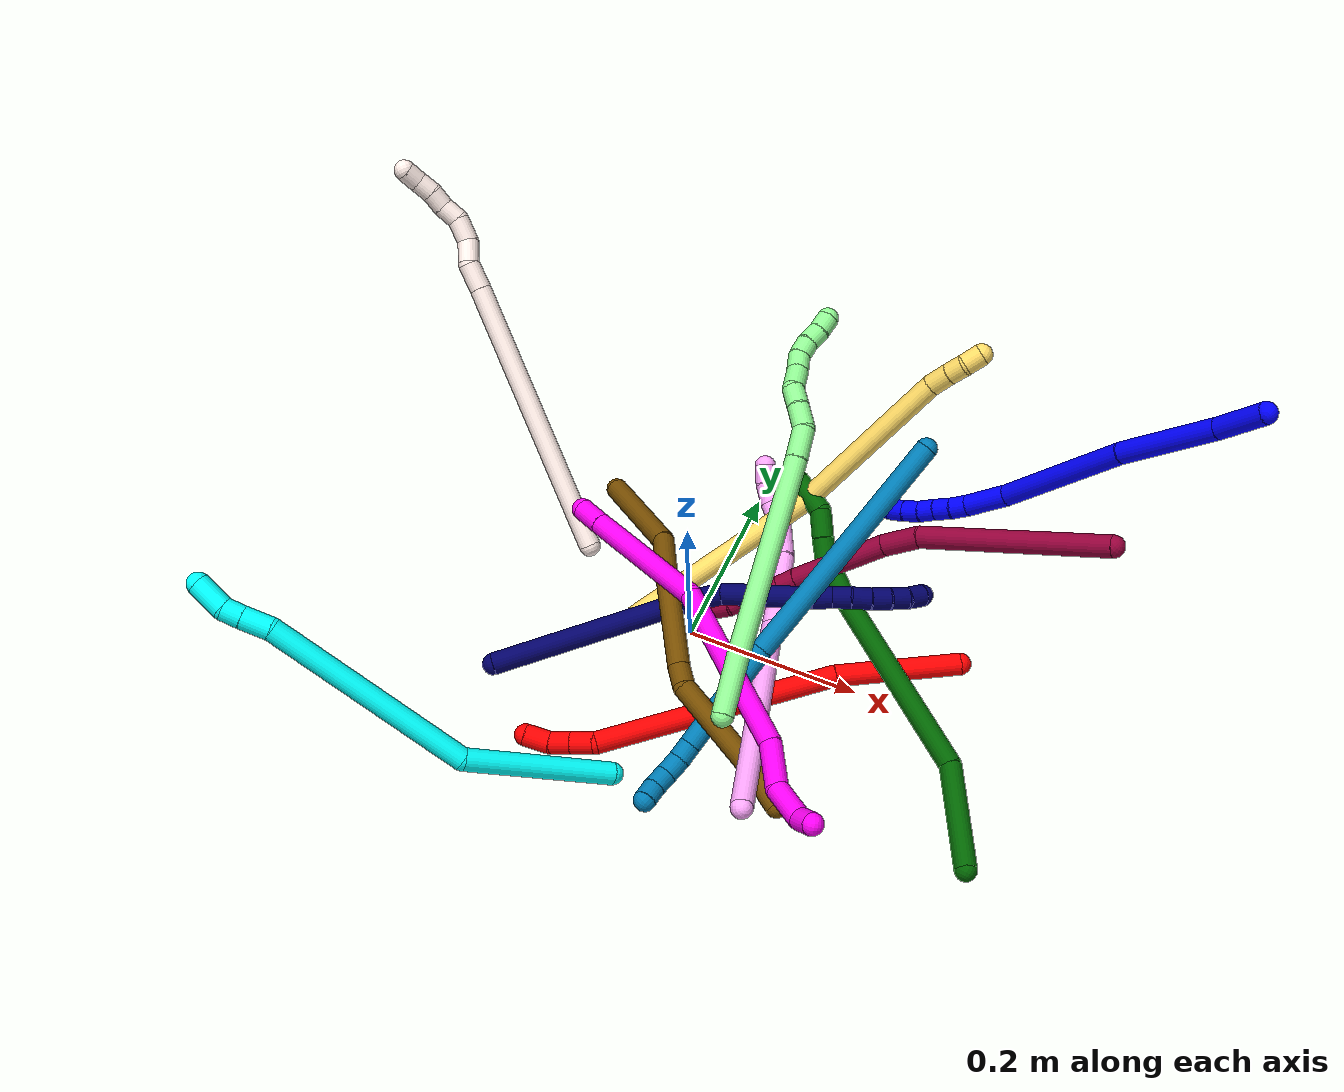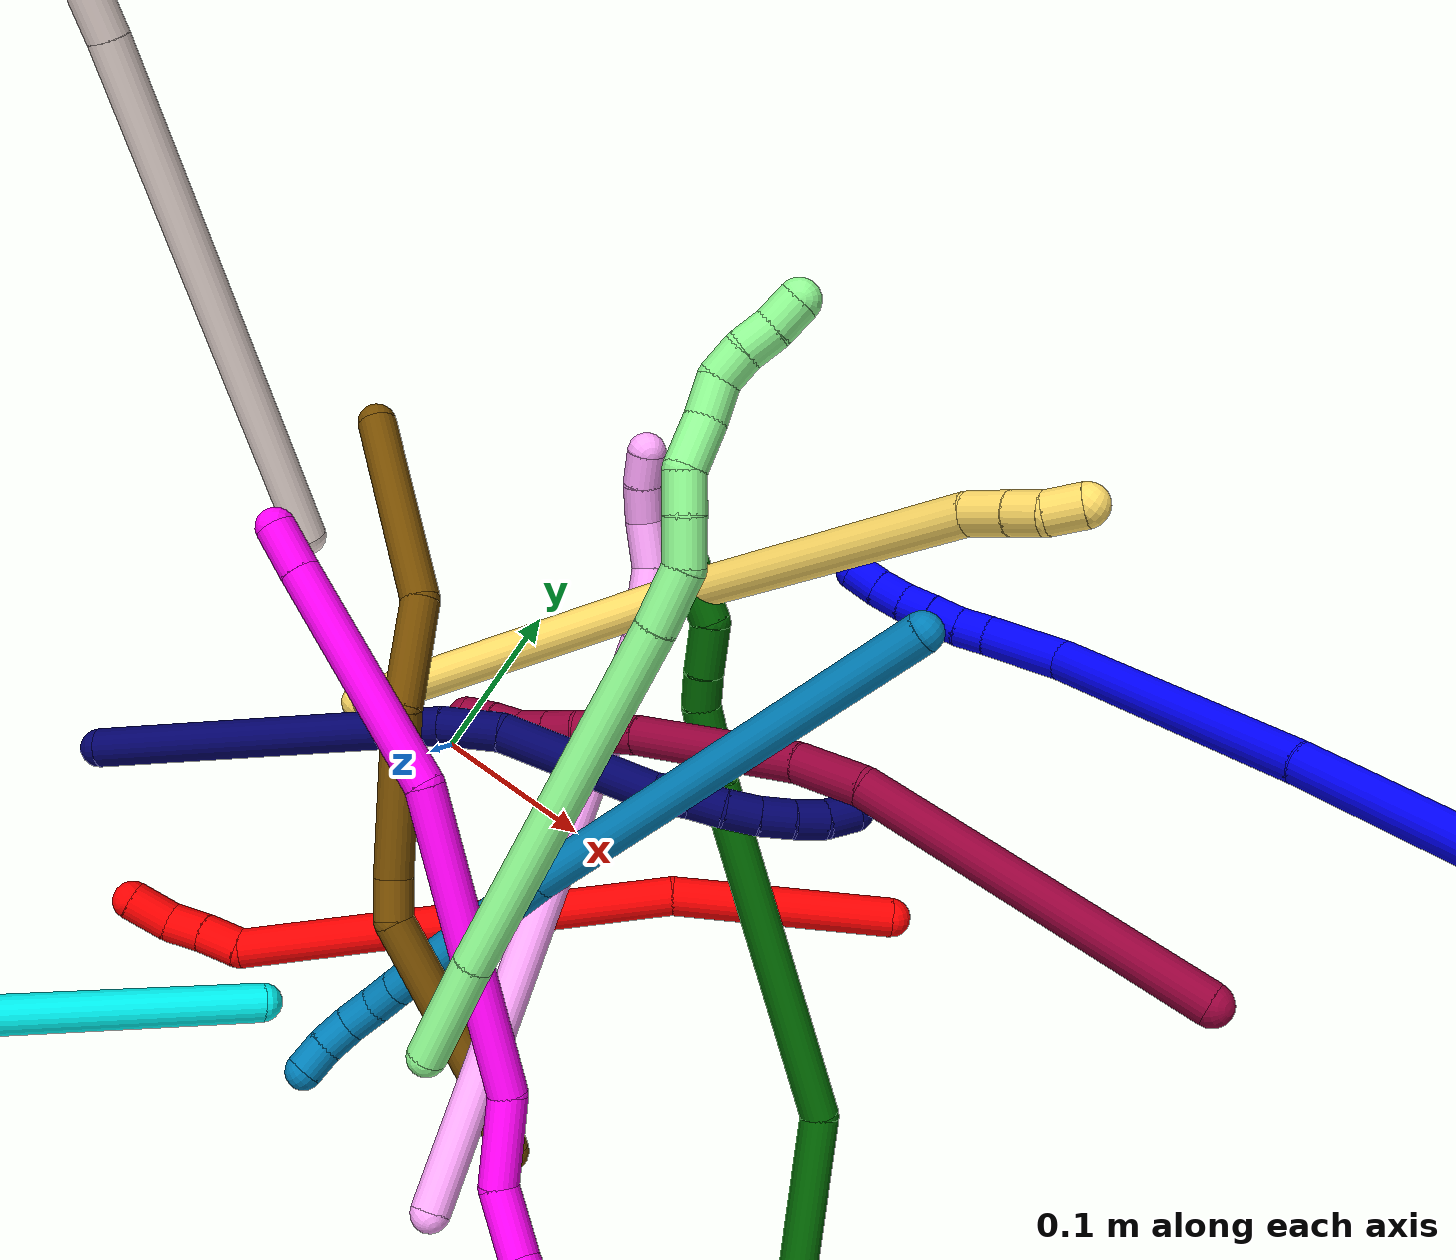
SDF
<sdf version="1.7">
 <world name="default">
  <plugin name="TubeGeneratorPlugin" filename="libtube_generator_plugin.so"/>
  <model name="photoneo_s_sensor">
   <static>1</static>
   <pose>0 0 2 1.57079 1.57079 3.14159</pose>
   <link name="link">
    <inertial><mass>0.1</mass></inertial>
    <sensor name="sensor" type="depth">
     <update_rate>30</update_rate>
     <camera>
      <horizontal_fov>1.22</horizontal_fov>
      <image><width>1920</width><height>1200</height><format>B8G8R8</format></image>
      <clip><near>0.1</near><far>4</far></clip>
      <depth_camera><output>points</output></depth_camera>
     </camera>
     <plugin name="camera_plugin" filename="libgazebo_ros_depth_camera.so">
      <baseline>0.2</baseline>
      <alwaysOn>1</alwaysOn>
      <updateRate>0.0</updateRate>
      <cameraName>camera_ir</cameraName>
      <imageTopicName>/camera/color/image_raw</imageTopicName>
      <cameraInfoTopicName>/camera/color/camera_info</cameraInfoTopicName>
      <depthImageTopicName>/camera/depth/image_raw</depthImageTopicName>
      <depthImageCameraInfoTopicName>/camera/depth/camera_info</depthImageCameraInfoTopicName>
      <pointCloudTopicName>/camera/depth/points</pointCloudTopicName>
      <frameName>fr_optical</frameName>
      <pointCloudCutoff>0.1</pointCloudCutoff>
      <pointCloudCutoffMax>2.0</pointCloudCutoffMax>
      <distortionK1>0</distortionK1>
      <distortionK2>0</distortionK2>
      <distortionK3>0</distortionK3>
      <distortionT1>0</distortionT1>
      <distortionT2>0</distortionT2>
      <CxPrime>0</CxPrime>
      <Cx>0</Cx>
      <Cy>0</Cy>
      <focalLength>0</focalLength>
      <hackBaseline>0</hackBaseline>
     </plugin>
    </sensor>
   </link>
  </model>
  <gravity>0 0 -9.8</gravity>
  <magnetic_field>6e-06 2.3e-05 -4.2e-05</magnetic_field>
  <atmosphere type="adiabatic"/>
  <physics name="default_physics" default="0" type="ode">
   <max_step_size>0.003</max_step_size>
   <real_time_factor>1</real_time_factor>
   <real_time_update_rate>1000</real_time_update_rate>
   <max_contacts>10000</max_contacts>
   <ode>
    <solver>
     <type>quick</type>
     <iters>100</iters>
     <sor>1.3</sor>
     <use_dynamic_moi_rescaling>0</use_dynamic_moi_rescaling>
    </solver>
    <constraints>
     <contact_max_correcting_vel>0</contact_max_correcting_vel>
     <contact_surface_layer>0.001</contact_surface_layer>
     <cfm>0</cfm>
     <erp>0.2</erp>
    </constraints>
   </ode>
  </physics>
  <scene><ambient>0.4 0.4 0.4 1</ambient><background>0.7 0.7 0.7 1</background><shadows>0</shadows></scene>
  <audio><device>default</device></audio>
  <spherical_coordinates>
   <surface_model>EARTH_WGS84</surface_model>
   <latitude_deg>0</latitude_deg>
   <longitude_deg>0</longitude_deg>
   <elevation>0</elevation>
   <heading_deg>0</heading_deg>
  </spherical_coordinates>
  <model name="bin">
   <static>1</static>
   <link name="bottom">
    <collision name="collision-bottom">
     <pose>0 0 -0.01 0 -0 0</pose>
     <geometry><box><size>0.8 0.6 0.02</size></box></geometry>
     <surface>
      <friction><ode><mu>100</mu><mu2>100</mu2></ode></friction>
      <contact><collide_bitmask>65535</collide_bitmask></contact>
     </surface>
    </collision>
   </link>
   <link name="west_wall">
    <collision name="collision-west_wall">
     <pose>-0.41 0 0.1 0 -0 0</pose>
     <geometry><box><size>0.02 0.6 0.2</size></box></geometry>
     <surface>
      <friction><ode><mu>100</mu><mu2>100</mu2></ode></friction>
      <contact><collide_bitmask>65535</collide_bitmask></contact>
     </surface>
    </collision>
   </link>
   <link name="east_wall">
    <collision name="collision-east_wall">
     <pose>0.41 0 0.1 0 -0 0</pose>
     <geometry><box><size>0.02 0.6 0.2</size></box></geometry>
     <surface>
      <friction><ode><mu>100</mu><mu2>100</mu2></ode></friction>
      <contact><collide_bitmask>65535</collide_bitmask></contact>
     </surface>
    </collision>
   </link>
   <link name="south_wall">
    <collision name="collision-south_wall">
     <pose>0 -0.31 0.1 0 -0 0</pose>
     <geometry><box><size>0.8 0.02 0.2</size></box></geometry>
     <surface>
      <friction><ode><mu>100</mu><mu2>100</mu2></ode></friction>
      <contact><collide_bitmask>65535</collide_bitmask></contact>
     </surface>
    </collision>
   </link>
   <link name="north_wall">
    <collision name="collision-north_wall">
     <pose>0 0.31 0.1 0 -0 0</pose>
     <geometry><box><size>0.8 0.02 0.2</size></box></geometry>
     <surface>
      <friction><ode><mu>100</mu><mu2>100</mu2></ode></friction>
      <contact><collide_bitmask>65535</collide_bitmask></contact>
     </surface>
    </collision>
   </link>
  </model>
  <model name="1">
   <static>0</static>
   <link name="1">
    <collision name="collision-cylinder-e_1_1_4">
     <pose>-0.020638 0.021391 0.005753 -1.30808 -0.750046 0.586164</pose>
     <geometry><cylinder><radius>0.0125</radius><length>0.06055</length></cylinder></geometry>
     <surface>
      <friction><ode><mu>1.16</mu><mu2>1.16</mu2><slip1>0</slip1><slip2>0</slip2></ode></friction>
      <contact><ode><kp>1e+06</kp><kd>1</kd><max_vel>0</max_vel><min_depth>0.001</min_depth></ode></contact>
     </surface>
    </collision>
    <visual name="visual-cylinder-e_1_1_4">
     <pose>-0.020638 0.021391 0.005753 -1.30808 -0.750046 0.586164</pose>
     <geometry><cylinder><radius>0.0125</radius><length>0.06055</length></cylinder></geometry>
     <material><ambient>0 0 1 1</ambient></material>
    </visual>
    <collision name="collision-cylinder-e_2_4_5">
     <pose>-0.086302 0.082443 0.020319 -1.35214 -0.836699 0.685168</pose>
     <geometry><cylinder><radius>0.0125</radius><length>0.121293</length></cylinder></geometry>
     <surface>
      <friction><ode><mu>1.16</mu><mu2>1.16</mu2><slip1>0</slip1><slip2>0</slip2></ode></friction>
      <contact><ode><kp>1e+06</kp><kd>1</kd><max_vel>0</max_vel><min_depth>0.001</min_depth></ode></contact>
     </surface>
    </collision>
    <visual name="visual-cylinder-e_2_4_5">
     <pose>-0.086302 0.082443 0.020319 -1.35214 -0.836699 0.685168</pose>
     <geometry><cylinder><radius>0.0125</radius><length>0.121293</length></cylinder></geometry>
     <material><ambient>0 0 1 1</ambient></material>
    </visual>
    <collision name="collision-cylinder-e_3_5_6">
     <pose>-0.187202 0.182562 0.041622 -1.36706 -0.735607 0.608257</pose>
     <geometry><cylinder><radius>0.0125</radius><length>0.166531</length></cylinder></geometry>
     <surface>
      <friction><ode><mu>1.16</mu><mu2>1.16</mu2><slip1>0</slip1><slip2>0</slip2></ode></friction>
      <contact><ode><kp>1e+06</kp><kd>1</kd><max_vel>0</max_vel><min_depth>0.001</min_depth></ode></contact>
     </surface>
    </collision>
    <visual name="visual-cylinder-e_3_5_6">
     <pose>-0.187202 0.182562 0.041622 -1.36706 -0.735607 0.608257</pose>
     <geometry><cylinder><radius>0.0125</radius><length>0.166531</length></cylinder></geometry>
     <material><ambient>0 0 1 1</ambient></material>
    </visual>
    <collision name="collision-cylinder-e_4_6_7">
     <pose>-0.263489 0.258653 0.053572 -1.60537 -0.916945 0.944677</pose>
     <geometry><cylinder><radius>0.0125</radius><length>0.051432</length></cylinder></geometry>
     <surface>
      <friction><ode><mu>1.16</mu><mu2>1.16</mu2><slip1>0</slip1><slip2>0</slip2></ode></friction>
      <contact><ode><kp>1e+06</kp><kd>1</kd><max_vel>0</max_vel><min_depth>0.001</min_depth></ode></contact>
     </surface>
    </collision>
    <visual name="visual-cylinder-e_4_6_7">
     <pose>-0.263489 0.258653 0.053572 -1.60537 -0.916945 0.944677</pose>
     <geometry><cylinder><radius>0.0125</radius><length>0.051432</length></cylinder></geometry>
     <material><ambient>0 0 1 1</ambient></material>
    </visual>
    <collision name="collision-cylinder-e_5_7_8">
     <pose>-0.292468 0.279344 0.051887 -1.79339 -1.0264 1.22866</pose>
     <geometry><cylinder><radius>0.0125</radius><length>0.020029</length></cylinder></geometry>
     <surface>
      <friction><ode><mu>1.16</mu><mu2>1.16</mu2><slip1>0</slip1><slip2>0</slip2></ode></friction>
      <contact><ode><kp>1e+06</kp><kd>1</kd><max_vel>0</max_vel><min_depth>0.001</min_depth></ode></contact>
     </surface>
    </collision>
    <visual name="visual-cylinder-e_5_7_8">
     <pose>-0.292468 0.279344 0.051887 -1.79339 -1.0264 1.22866</pose>
     <geometry><cylinder><radius>0.0125</radius><length>0.020029</length></cylinder></geometry>
     <material><ambient>0 0 1 1</ambient></material>
    </visual>
    <collision name="collision-cylinder-e_6_8_9">
     <pose>-0.309972 0.289048 0.050832 -1.55131 -1.09143 1.07421</pose>
     <geometry><cylinder><radius>0.0125</radius><length>0.020146</length></cylinder></geometry>
     <surface>
      <friction><ode><mu>1.16</mu><mu2>1.16</mu2><slip1>0</slip1><slip2>0</slip2></ode></friction>
      <contact><ode><kp>1e+06</kp><kd>1</kd><max_vel>0</max_vel><min_depth>0.001</min_depth></ode></contact>
     </surface>
    </collision>
    <visual name="visual-cylinder-e_6_8_9">
     <pose>-0.309972 0.289048 0.050832 -1.55131 -1.09143 1.07421</pose>
     <geometry><cylinder><radius>0.0125</radius><length>0.020146</length></cylinder></geometry>
     <material><ambient>0 0 1 1</ambient></material>
    </visual>
    <collision name="collision-cylinder-e_7_9_10">
     <pose>-0.327579 0.298693 0.050894 -1.57656 -1.04761 1.05261</pose>
     <geometry><cylinder><radius>0.0125</radius><length>0.020016</length></cylinder></geometry>
     <surface>
      <friction><ode><mu>1.16</mu><mu2>1.16</mu2><slip1>0</slip1><slip2>0</slip2></ode></friction>
      <contact><ode><kp>1e+06</kp><kd>1</kd><max_vel>0</max_vel><min_depth>0.001</min_depth></ode></contact>
     </surface>
    </collision>
    <visual name="visual-cylinder-e_7_9_10">
     <pose>-0.327579 0.298693 0.050894 -1.57656 -1.04761 1.05261</pose>
     <geometry><cylinder><radius>0.0125</radius><length>0.020016</length></cylinder></geometry>
     <material><ambient>0 0 1 1</ambient></material>
    </visual>
    <collision name="collision-cylinder-e_8_10_11">
     <pose>-0.345413 0.307647 0.051481 -1.41634 -1.15911 1.02175</pose>
     <geometry><cylinder><radius>0.0125</radius><length>0.020001</length></cylinder></geometry>
     <surface>
      <friction><ode><mu>1.16</mu><mu2>1.16</mu2><slip1>0</slip1><slip2>0</slip2></ode></friction>
      <contact><ode><kp>1e+06</kp><kd>1</kd><max_vel>0</max_vel><min_depth>0.001</min_depth></ode></contact>
     </surface>
    </collision>
    <visual name="visual-cylinder-e_8_10_11">
     <pose>-0.345413 0.307647 0.051481 -1.41634 -1.15911 1.02175</pose>
     <geometry><cylinder><radius>0.0125</radius><length>0.020001</length></cylinder></geometry>
     <material><ambient>0 0 1 1</ambient></material>
    </visual>
    <collision name="collision-cylinder-e_9_11_2">
     <pose>-0.363948 0.314843 0.053401 -1.18817 -1.2139 0.877162</pose>
     <geometry><cylinder><radius>0.0125</radius><length>0.020001</length></cylinder></geometry>
     <surface>
      <friction><ode><mu>1.16</mu><mu2>1.16</mu2><slip1>0</slip1><slip2>0</slip2></ode></friction>
      <contact><ode><kp>1e+06</kp><kd>1</kd><max_vel>0</max_vel><min_depth>0.001</min_depth></ode></contact>
     </surface>
    </collision>
    <visual name="visual-cylinder-e_9_11_2">
     <pose>-0.363948 0.314843 0.053401 -1.18817 -1.2139 0.877162</pose>
     <geometry><cylinder><radius>0.0125</radius><length>0.020001</length></cylinder></geometry>
     <material><ambient>0 0 1 1</ambient></material>
    </visual>
    <collision name="collision-sphere-2">
     <pose>-0.373318 0.318084 0.054705 0 -0 0</pose>
     <geometry><sphere><radius>0.0125</radius></sphere></geometry>
     <surface>
      <friction><ode><mu>1.16</mu><mu2>1.16</mu2><slip1>0</slip1><slip2>0</slip2></ode></friction>
      <contact><ode><kp>1e+06</kp><kd>1</kd><max_vel>0</max_vel><min_depth>0.001</min_depth></ode></contact>
     </surface>
    </collision>
    <visual name="visual-sphere-2">
     <pose>-0.373318 0.318084 0.054705 0 -0 0</pose>
     <geometry><sphere><radius>0.0125</radius></sphere></geometry>
     <material><ambient>0 0 1 1</ambient></material>
    </visual>
    <collision name="collision-sphere-11">
     <pose>-0.354578 0.311601 0.052096 0 -0 0</pose>
     <geometry><sphere><radius>0.0125</radius></sphere></geometry>
     <surface>
      <friction><ode><mu>1.16</mu><mu2>1.16</mu2><slip1>0</slip1><slip2>0</slip2></ode></friction>
      <contact><ode><kp>1e+06</kp><kd>1</kd><max_vel>0</max_vel><min_depth>0.001</min_depth></ode></contact>
     </surface>
    </collision>
    <visual name="visual-sphere-11">
     <pose>-0.354578 0.311601 0.052096 0 -0 0</pose>
     <geometry><sphere><radius>0.0125</radius></sphere></geometry>
     <material><ambient>0 0 1 1</ambient></material>
    </visual>
    <collision name="collision-sphere-10">
     <pose>-0.336248 0.303693 0.050865 0 -0 0</pose>
     <geometry><sphere><radius>0.0125</radius></sphere></geometry>
     <surface>
      <friction><ode><mu>1.16</mu><mu2>1.16</mu2><slip1>0</slip1><slip2>0</slip2></ode></friction>
      <contact><ode><kp>1e+06</kp><kd>1</kd><max_vel>0</max_vel><min_depth>0.001</min_depth></ode></contact>
     </surface>
    </collision>
    <visual name="visual-sphere-10">
     <pose>-0.336248 0.303693 0.050865 0 -0 0</pose>
     <geometry><sphere><radius>0.0125</radius></sphere></geometry>
     <material><ambient>0 0 1 1</ambient></material>
    </visual>
    <collision name="collision-sphere-9">
     <pose>-0.31891 0.293693 0.050923 0 -0 0</pose>
     <geometry><sphere><radius>0.0125</radius></sphere></geometry>
     <surface>
      <friction><ode><mu>1.16</mu><mu2>1.16</mu2><slip1>0</slip1><slip2>0</slip2></ode></friction>
      <contact><ode><kp>1e+06</kp><kd>1</kd><max_vel>0</max_vel><min_depth>0.001</min_depth></ode></contact>
     </surface>
    </collision>
    <visual name="visual-sphere-9">
     <pose>-0.31891 0.293693 0.050923 0 -0 0</pose>
     <geometry><sphere><radius>0.0125</radius></sphere></geometry>
     <material><ambient>0 0 1 1</ambient></material>
    </visual>
    <collision name="collision-sphere-4">
     <pose>-0.041275 0.042782 0.011506 0 -0 0</pose>
     <geometry><sphere><radius>0.0125</radius></sphere></geometry>
     <surface>
      <friction><ode><mu>1.16</mu><mu2>1.16</mu2><slip1>0</slip1><slip2>0</slip2></ode></friction>
      <contact><ode><kp>1e+06</kp><kd>1</kd><max_vel>0</max_vel><min_depth>0.001</min_depth></ode></contact>
     </surface>
    </collision>
    <visual name="visual-sphere-4">
     <pose>-0.041275 0.042782 0.011506 0 -0 0</pose>
     <geometry><sphere><radius>0.0125</radius></sphere></geometry>
     <material><ambient>0 0 1 1</ambient></material>
    </visual>
    <collision name="collision-sphere-1">
     <geometry><sphere><radius>0.0125</radius></sphere></geometry>
     <surface>
      <friction><ode><mu>1.16</mu><mu2>1.16</mu2><slip1>0</slip1><slip2>0</slip2></ode></friction>
      <contact><ode><kp>1e+06</kp><kd>1</kd><max_vel>0</max_vel><min_depth>0.001</min_depth></ode></contact>
     </surface>
    </collision>
    <visual name="visual-sphere-1">
     <geometry><sphere><radius>0.0125</radius></sphere></geometry>
     <material><ambient>0 0 1 1</ambient></material>
    </visual>
    <collision name="collision-sphere-8">
     <pose>-0.301035 0.284403 0.050742 0 -0 0</pose>
     <geometry><sphere><radius>0.0125</radius></sphere></geometry>
     <surface>
      <friction><ode><mu>1.16</mu><mu2>1.16</mu2><slip1>0</slip1><slip2>0</slip2></ode></friction>
      <contact><ode><kp>1e+06</kp><kd>1</kd><max_vel>0</max_vel><min_depth>0.001</min_depth></ode></contact>
     </surface>
    </collision>
    <visual name="visual-sphere-8">
     <pose>-0.301035 0.284403 0.050742 0 -0 0</pose>
     <geometry><sphere><radius>0.0125</radius></sphere></geometry>
     <material><ambient>0 0 1 1</ambient></material>
    </visual>
    <collision name="collision-sphere-5">
     <pose>-0.131328 0.122104 0.029131 0 -0 0</pose>
     <geometry><sphere><radius>0.0125</radius></sphere></geometry>
     <surface>
      <friction><ode><mu>1.16</mu><mu2>1.16</mu2><slip1>0</slip1><slip2>0</slip2></ode></friction>
      <contact><ode><kp>1e+06</kp><kd>1</kd><max_vel>0</max_vel><min_depth>0.001</min_depth></ode></contact>
     </surface>
    </collision>
    <visual name="visual-sphere-5">
     <pose>-0.131328 0.122104 0.029131 0 -0 0</pose>
     <geometry><sphere><radius>0.0125</radius></sphere></geometry>
     <material><ambient>0 0 1 1</ambient></material>
    </visual>
    <collision name="collision-sphere-6">
     <pose>-0.243077 0.24302 0.054113 0 -0 0</pose>
     <geometry><sphere><radius>0.0125</radius></sphere></geometry>
     <surface>
      <friction><ode><mu>1.16</mu><mu2>1.16</mu2><slip1>0</slip1><slip2>0</slip2></ode></friction>
      <contact><ode><kp>1e+06</kp><kd>1</kd><max_vel>0</max_vel><min_depth>0.001</min_depth></ode></contact>
     </surface>
    </collision>
    <visual name="visual-sphere-6">
     <pose>-0.243077 0.24302 0.054113 0 -0 0</pose>
     <geometry><sphere><radius>0.0125</radius></sphere></geometry>
     <material><ambient>0 0 1 1</ambient></material>
    </visual>
    <collision name="collision-sphere-7">
     <pose>-0.283901 0.274285 0.053032 0 -0 0</pose>
     <geometry><sphere><radius>0.0125</radius></sphere></geometry>
     <surface>
      <friction><ode><mu>1.16</mu><mu2>1.16</mu2><slip1>0</slip1><slip2>0</slip2></ode></friction>
      <contact><ode><kp>1e+06</kp><kd>1</kd><max_vel>0</max_vel><min_depth>0.001</min_depth></ode></contact>
     </surface>
    </collision>
    <visual name="visual-sphere-7">
     <pose>-0.283901 0.274285 0.053032 0 -0 0</pose>
     <geometry><sphere><radius>0.0125</radius></sphere></geometry>
     <material><ambient>0 0 1 1</ambient></material>
    </visual>
    <inertial>
     <pose>-0.178583 0.169695 0.035359 0 -0 0</pose>
     <mass>0.5</mass>
     <inertia><ixx>0.000556</ixx><ixy>0</ixy><ixz>0</ixz><iyy>0.000608</iyy><iyz>0</iyz><izz>2e-06</izz></inertia>
    </inertial>
   </link>
   <pose>0.524957 0.285271 0.331206 -1.88011 0.004391 -0.009671</pose>
  </model>
  <model name="2">
   <static>0</static>
   <link name="2">
    <collision name="collision-cylinder-e_1_1_4">
     <pose>-0.042229 -0.039448 0.041165 0.764108 -0.637508 -0.263654</pose>
     <geometry><cylinder><radius>0.0125</radius><length>0.141901</length></cylinder></geometry>
     <surface>
      <friction><ode><mu>1.16</mu><mu2>1.16</mu2><slip1>0</slip1><slip2>0</slip2></ode></friction>
      <contact><ode><kp>1e+06</kp><kd>1</kd><max_vel>0</max_vel><min_depth>0.001</min_depth></ode></contact>
     </surface>
    </collision>
    <visual name="visual-cylinder-e_1_1_4">
     <pose>-0.042229 -0.039448 0.041165 0.764108 -0.637508 -0.263654</pose>
     <geometry><cylinder><radius>0.0125</radius><length>0.141901</length></cylinder></geometry>
     <material><ambient>1 0 0 1</ambient></material>
    </visual>
    <collision name="collision-cylinder-e_2_4_5">
     <pose>-0.142132 -0.172266 0.168196 0.827233 -0.426721 -0.189629</pose>
     <geometry><cylinder><radius>0.0125</radius><length>0.278691</length></cylinder></geometry>
     <surface>
      <friction><ode><mu>1.16</mu><mu2>1.16</mu2><slip1>0</slip1><slip2>0</slip2></ode></friction>
      <contact><ode><kp>1e+06</kp><kd>1</kd><max_vel>0</max_vel><min_depth>0.001</min_depth></ode></contact>
     </surface>
    </collision>
    <visual name="visual-cylinder-e_2_4_5">
     <pose>-0.142132 -0.172266 0.168196 0.827233 -0.426721 -0.189629</pose>
     <geometry><cylinder><radius>0.0125</radius><length>0.278691</length></cylinder></geometry>
     <material><ambient>1 0 0 1</ambient></material>
    </visual>
    <collision name="collision-cylinder-e_3_5_6">
     <pose>-0.210609 -0.271937 0.258849 0.921213 -0.938615 -0.493011</pose>
     <geometry><cylinder><radius>0.0125</radius><length>0.026783</length></cylinder></geometry>
     <surface>
      <friction><ode><mu>1.16</mu><mu2>1.16</mu2><slip1>0</slip1><slip2>0</slip2></ode></friction>
      <contact><ode><kp>1e+06</kp><kd>1</kd><max_vel>0</max_vel><min_depth>0.001</min_depth></ode></contact>
     </surface>
    </collision>
    <visual name="visual-cylinder-e_3_5_6">
     <pose>-0.210609 -0.271937 0.258849 0.921213 -0.938615 -0.493011</pose>
     <geometry><cylinder><radius>0.0125</radius><length>0.026783</length></cylinder></geometry>
     <material><ambient>1 0 0 1</ambient></material>
    </visual>
    <collision name="collision-cylinder-e_4_6_7">
     <pose>-0.230439 -0.284238 0.268657 0.873883 -0.856595 -0.420181</pose>
     <geometry><cylinder><radius>0.0125</radius><length>0.023891</length></cylinder></geometry>
     <surface>
      <friction><ode><mu>1.16</mu><mu2>1.16</mu2><slip1>0</slip1><slip2>0</slip2></ode></friction>
      <contact><ode><kp>1e+06</kp><kd>1</kd><max_vel>0</max_vel><min_depth>0.001</min_depth></ode></contact>
     </surface>
    </collision>
    <visual name="visual-cylinder-e_4_6_7">
     <pose>-0.230439 -0.284238 0.268657 0.873883 -0.856595 -0.420181</pose>
     <geometry><cylinder><radius>0.0125</radius><length>0.023891</length></cylinder></geometry>
     <material><ambient>1 0 0 1</ambient></material>
    </visual>
    <collision name="collision-cylinder-e_5_7_2">
     <pose>-0.251486 -0.293252 0.280948 0.393015 -0.991182 -0.214413</pose>
     <geometry><cylinder><radius>0.0125</radius><length>0.028733</length></cylinder></geometry>
     <surface>
      <friction><ode><mu>1.16</mu><mu2>1.16</mu2><slip1>0</slip1><slip2>0</slip2></ode></friction>
      <contact><ode><kp>1e+06</kp><kd>1</kd><max_vel>0</max_vel><min_depth>0.001</min_depth></ode></contact>
     </surface>
    </collision>
    <visual name="visual-cylinder-e_5_7_2">
     <pose>-0.251486 -0.293252 0.280948 0.393015 -0.991182 -0.214413</pose>
     <geometry><cylinder><radius>0.0125</radius><length>0.028733</length></cylinder></geometry>
     <material><ambient>1 0 0 1</ambient></material>
    </visual>
    <collision name="collision-sphere-2">
     <pose>-0.263506 -0.296265 0.288217 0 -0 0</pose>
     <geometry><sphere><radius>0.0125</radius></sphere></geometry>
     <surface>
      <friction><ode><mu>1.16</mu><mu2>1.16</mu2><slip1>0</slip1><slip2>0</slip2></ode></friction>
      <contact><ode><kp>1e+06</kp><kd>1</kd><max_vel>0</max_vel><min_depth>0.001</min_depth></ode></contact>
     </surface>
    </collision>
    <visual name="visual-sphere-2">
     <pose>-0.263506 -0.296265 0.288217 0 -0 0</pose>
     <geometry><sphere><radius>0.0125</radius></sphere></geometry>
     <material><ambient>1 0 0 1</ambient></material>
    </visual>
    <collision name="collision-sphere-7">
     <pose>-0.239466 -0.290238 0.27368 0 -0 0</pose>
     <geometry><sphere><radius>0.0125</radius></sphere></geometry>
     <surface>
      <friction><ode><mu>1.16</mu><mu2>1.16</mu2><slip1>0</slip1><slip2>0</slip2></ode></friction>
      <contact><ode><kp>1e+06</kp><kd>1</kd><max_vel>0</max_vel><min_depth>0.001</min_depth></ode></contact>
     </surface>
    </collision>
    <visual name="visual-sphere-7">
     <pose>-0.239466 -0.290238 0.27368 0 -0 0</pose>
     <geometry><sphere><radius>0.0125</radius></sphere></geometry>
     <material><ambient>1 0 0 1</ambient></material>
    </visual>
    <collision name="collision-sphere-6">
     <pose>-0.221413 -0.278238 0.263635 0 -0 0</pose>
     <geometry><sphere><radius>0.0125</radius></sphere></geometry>
     <surface>
      <friction><ode><mu>1.16</mu><mu2>1.16</mu2><slip1>0</slip1><slip2>0</slip2></ode></friction>
      <contact><ode><kp>1e+06</kp><kd>1</kd><max_vel>0</max_vel><min_depth>0.001</min_depth></ode></contact>
     </surface>
    </collision>
    <visual name="visual-sphere-6">
     <pose>-0.221413 -0.278238 0.263635 0 -0 0</pose>
     <geometry><sphere><radius>0.0125</radius></sphere></geometry>
     <material><ambient>1 0 0 1</ambient></material>
    </visual>
    <collision name="collision-sphere-5">
     <pose>-0.199806 -0.265635 0.254063 0 -0 0</pose>
     <geometry><sphere><radius>0.0125</radius></sphere></geometry>
     <surface>
      <friction><ode><mu>1.16</mu><mu2>1.16</mu2><slip1>0</slip1><slip2>0</slip2></ode></friction>
      <contact><ode><kp>1e+06</kp><kd>1</kd><max_vel>0</max_vel><min_depth>0.001</min_depth></ode></contact>
     </surface>
    </collision>
    <visual name="visual-sphere-5">
     <pose>-0.199806 -0.265635 0.254063 0 -0 0</pose>
     <geometry><sphere><radius>0.0125</radius></sphere></geometry>
     <material><ambient>1 0 0 1</ambient></material>
    </visual>
    <collision name="collision-sphere-1">
     <geometry><sphere><radius>0.0125</radius></sphere></geometry>
     <surface>
      <friction><ode><mu>1.16</mu><mu2>1.16</mu2><slip1>0</slip1><slip2>0</slip2></ode></friction>
      <contact><ode><kp>1e+06</kp><kd>1</kd><max_vel>0</max_vel><min_depth>0.001</min_depth></ode></contact>
     </surface>
    </collision>
    <visual name="visual-sphere-1">
     <geometry><sphere><radius>0.0125</radius></sphere></geometry>
     <material><ambient>1 0 0 1</ambient></material>
    </visual>
    <collision name="collision-sphere-4">
     <pose>-0.084459 -0.078896 0.082329 0 -0 0</pose>
     <geometry><sphere><radius>0.0125</radius></sphere></geometry>
     <surface>
      <friction><ode><mu>1.16</mu><mu2>1.16</mu2><slip1>0</slip1><slip2>0</slip2></ode></friction>
      <contact><ode><kp>1e+06</kp><kd>1</kd><max_vel>0</max_vel><min_depth>0.001</min_depth></ode></contact>
     </surface>
    </collision>
    <visual name="visual-sphere-4">
     <pose>-0.084459 -0.078896 0.082329 0 -0 0</pose>
     <geometry><sphere><radius>0.0125</radius></sphere></geometry>
     <material><ambient>1 0 0 1</ambient></material>
    </visual>
    <inertial>
     <pose>-0.127951 -0.152214 0.14828 0 -0 0</pose>
     <mass>0.5</mass>
     <inertia>
      <ixx>0.001431</ixx>
      <ixy>0</ixy>
      <ixz>0</ixz>
      <iyy>0.001126</iyy>
      <iyz>0</iyz>
      <izz>0.002279</izz>
     </inertia>
    </inertial>
   </link>
   <pose>0.297724 0.0742 0.012527 0.572448 -0.298946 -0.380777</pose>
  </model>
  <model name="3">
   <static>0</static>
   <link name="3">
    <collision name="collision-cylinder-e_1_1_4">
     <pose>0.000725 -0.002177 0.08595 0.025323 0.00843 0.000107</pose>
     <geometry><cylinder><radius>0.0125</radius><length>0.171961</length></cylinder></geometry>
     <surface>
      <friction><ode><mu>1.16</mu><mu2>1.16</mu2><slip1>0</slip1><slip2>0</slip2></ode></friction>
      <contact><ode><kp>1e+06</kp><kd>1</kd><max_vel>0</max_vel><min_depth>0.001</min_depth></ode></contact>
     </surface>
    </collision>
    <visual name="visual-cylinder-e_1_1_4">
     <pose>0.000725 -0.002177 0.08595 0.025323 0.00843 0.000107</pose>
     <geometry><cylinder><radius>0.0125</radius><length>0.171961</length></cylinder></geometry>
     <material><ambient>0.003922 1 0.996078 1</ambient></material>
    </visual>
    <collision name="collision-cylinder-e_2_4_5">
     <pose>0.047034 -0.04444 0.274758 0.371615 0.391603 0.074533</pose>
     <geometry><cylinder><radius>0.0125</radius><length>0.238869</length></cylinder></geometry>
     <surface>
      <friction><ode><mu>1.16</mu><mu2>1.16</mu2><slip1>0</slip1><slip2>0</slip2></ode></friction>
      <contact><ode><kp>1e+06</kp><kd>1</kd><max_vel>0</max_vel><min_depth>0.001</min_depth></ode></contact>
     </surface>
    </collision>
    <visual name="visual-cylinder-e_2_4_5">
     <pose>0.047034 -0.04444 0.274758 0.371615 0.391603 0.074533</pose>
     <geometry><cylinder><radius>0.0125</radius><length>0.238869</length></cylinder></geometry>
     <material><ambient>0.003922 1 0.996078 1</ambient></material>
    </visual>
    <collision name="collision-cylinder-e_3_5_6">
     <pose>0.099852 -0.085327 0.391657 0.056994 0.475008 0.0138</pose>
     <geometry><cylinder><radius>0.0125</radius><length>0.03163</length></cylinder></geometry>
     <surface>
      <friction><ode><mu>1.16</mu><mu2>1.16</mu2><slip1>0</slip1><slip2>0</slip2></ode></friction>
      <contact><ode><kp>1e+06</kp><kd>1</kd><max_vel>0</max_vel><min_depth>0.001</min_depth></ode></contact>
     </surface>
    </collision>
    <visual name="visual-cylinder-e_3_5_6">
     <pose>0.099852 -0.085327 0.391657 0.056994 0.475008 0.0138</pose>
     <geometry><cylinder><radius>0.0125</radius><length>0.03163</length></cylinder></geometry>
     <material><ambient>0.003922 1 0.996078 1</ambient></material>
    </visual>
    <collision name="collision-cylinder-e_4_6_7">
     <pose>0.112211 -0.087041 0.414814 0.099832 0.510179 0.026053</pose>
     <geometry><cylinder><radius>0.0125</radius><length>0.020995</length></cylinder></geometry>
     <surface>
      <friction><ode><mu>1.16</mu><mu2>1.16</mu2><slip1>0</slip1><slip2>0</slip2></ode></friction>
      <contact><ode><kp>1e+06</kp><kd>1</kd><max_vel>0</max_vel><min_depth>0.001</min_depth></ode></contact>
     </surface>
    </collision>
    <visual name="visual-cylinder-e_4_6_7">
     <pose>0.112211 -0.087041 0.414814 0.099832 0.510179 0.026053</pose>
     <geometry><cylinder><radius>0.0125</radius><length>0.020995</length></cylinder></geometry>
     <material><ambient>0.003922 1 0.996078 1</ambient></material>
    </visual>
    <collision name="collision-cylinder-e_5_7_2">
     <pose>0.129505 -0.093807 0.436241 0.443734 0.728673 0.171633</pose>
     <geometry><cylinder><radius>0.0125</radius><length>0.036544</length></cylinder></geometry>
     <surface>
      <friction><ode><mu>1.16</mu><mu2>1.16</mu2><slip1>0</slip1><slip2>0</slip2></ode></friction>
      <contact><ode><kp>1e+06</kp><kd>1</kd><max_vel>0</max_vel><min_depth>0.001</min_depth></ode></contact>
     </surface>
    </collision>
    <visual name="visual-cylinder-e_5_7_2">
     <pose>0.129505 -0.093807 0.436241 0.443734 0.728673 0.171633</pose>
     <geometry><cylinder><radius>0.0125</radius><length>0.036544</length></cylinder></geometry>
     <material><ambient>0.003922 1 0.996078 1</ambient></material>
    </visual>
    <collision name="collision-sphere-2">
     <pose>0.141672 -0.099659 0.448553 0 -0 0</pose>
     <geometry><sphere><radius>0.0125</radius></sphere></geometry>
     <surface>
      <friction><ode><mu>1.16</mu><mu2>1.16</mu2><slip1>0</slip1><slip2>0</slip2></ode></friction>
      <contact><ode><kp>1e+06</kp><kd>1</kd><max_vel>0</max_vel><min_depth>0.001</min_depth></ode></contact>
     </surface>
    </collision>
    <visual name="visual-sphere-2">
     <pose>0.141672 -0.099659 0.448553 0 -0 0</pose>
     <geometry><sphere><radius>0.0125</radius></sphere></geometry>
     <material><ambient>0.003922 1 0.996078 1</ambient></material>
    </visual>
    <collision name="collision-sphere-7">
     <pose>0.117338 -0.087954 0.423929 0 -0 0</pose>
     <geometry><sphere><radius>0.0125</radius></sphere></geometry>
     <surface>
      <friction><ode><mu>1.16</mu><mu2>1.16</mu2><slip1>0</slip1><slip2>0</slip2></ode></friction>
      <contact><ode><kp>1e+06</kp><kd>1</kd><max_vel>0</max_vel><min_depth>0.001</min_depth></ode></contact>
     </surface>
    </collision>
    <visual name="visual-sphere-7">
     <pose>0.117338 -0.087954 0.423929 0 -0 0</pose>
     <geometry><sphere><radius>0.0125</radius></sphere></geometry>
     <material><ambient>0.003922 1 0.996078 1</ambient></material>
    </visual>
    <collision name="collision-sphere-6">
     <pose>0.107085 -0.086128 0.405698 0 -0 0</pose>
     <geometry><sphere><radius>0.0125</radius></sphere></geometry>
     <surface>
      <friction><ode><mu>1.16</mu><mu2>1.16</mu2><slip1>0</slip1><slip2>0</slip2></ode></friction>
      <contact><ode><kp>1e+06</kp><kd>1</kd><max_vel>0</max_vel><min_depth>0.001</min_depth></ode></contact>
     </surface>
    </collision>
    <visual name="visual-sphere-6">
     <pose>0.107085 -0.086128 0.405698 0 -0 0</pose>
     <geometry><sphere><radius>0.0125</radius></sphere></geometry>
     <material><ambient>0.003922 1 0.996078 1</ambient></material>
    </visual>
    <collision name="collision-sphere-5">
     <pose>0.092619 -0.084526 0.377616 0 -0 0</pose>
     <geometry><sphere><radius>0.0125</radius></sphere></geometry>
     <surface>
      <friction><ode><mu>1.16</mu><mu2>1.16</mu2><slip1>0</slip1><slip2>0</slip2></ode></friction>
      <contact><ode><kp>1e+06</kp><kd>1</kd><max_vel>0</max_vel><min_depth>0.001</min_depth></ode></contact>
     </surface>
    </collision>
    <visual name="visual-sphere-5">
     <pose>0.092619 -0.084526 0.377616 0 -0 0</pose>
     <geometry><sphere><radius>0.0125</radius></sphere></geometry>
     <material><ambient>0.003922 1 0.996078 1</ambient></material>
    </visual>
    <collision name="collision-sphere-1">
     <geometry><sphere><radius>0.0125</radius></sphere></geometry>
     <surface>
      <friction><ode><mu>1.16</mu><mu2>1.16</mu2><slip1>0</slip1><slip2>0</slip2></ode></friction>
      <contact><ode><kp>1e+06</kp><kd>1</kd><max_vel>0</max_vel><min_depth>0.001</min_depth></ode></contact>
     </surface>
    </collision>
    <visual name="visual-sphere-1">
     <geometry><sphere><radius>0.0125</radius></sphere></geometry>
     <material><ambient>0.003922 1 0.996078 1</ambient></material>
    </visual>
    <collision name="collision-sphere-4">
     <pose>0.00145 -0.004354 0.1719 0 -0 0</pose>
     <geometry><sphere><radius>0.0125</radius></sphere></geometry>
     <surface>
      <friction><ode><mu>1.16</mu><mu2>1.16</mu2><slip1>0</slip1><slip2>0</slip2></ode></friction>
      <contact><ode><kp>1e+06</kp><kd>1</kd><max_vel>0</max_vel><min_depth>0.001</min_depth></ode></contact>
     </surface>
    </collision>
    <visual name="visual-sphere-4">
     <pose>0.00145 -0.004354 0.1719 0 -0 0</pose>
     <geometry><sphere><radius>0.0125</radius></sphere></geometry>
     <material><ambient>0.003922 1 0.996078 1</ambient></material>
    </visual>
    <inertial>
     <pose>0.043213 -0.037888 0.234901 0 -0 0</pose>
     <mass>0.5</mass>
     <inertia>
      <ixx>0.001586</ixx>
      <ixy>0</ixy>
      <ixz>0</ixz>
      <iyy>0.001589</iyy>
      <iyz>0</iyz>
      <izz>-1.5e-05</izz>
     </inertia>
    </inertial>
   </link>
   <pose>-0.001998 -0.204661 0.011865 -1.08994 0.363291 2.34488</pose>
  </model>
  <model name="4">
   <static>0</static>
   <link name="4">
    <collision name="collision-cylinder-e_1_1_4">
     <pose>-0.02738 0.111047 -0.077835 -2.18214 -0.199224 0.379577</pose>
     <geometry><cylinder><radius>0.0125</radius><length>0.276691</length></cylinder></geometry>
     <surface>
      <friction><ode><mu>1.16</mu><mu2>1.16</mu2><slip1>0</slip1><slip2>0</slip2></ode></friction>
      <contact><ode><kp>1e+06</kp><kd>1</kd><max_vel>0</max_vel><min_depth>0.001</min_depth></ode></contact>
     </surface>
    </collision>
    <visual name="visual-cylinder-e_1_1_4">
     <pose>-0.02738 0.111047 -0.077835 -2.18214 -0.199224 0.379577</pose>
     <geometry><cylinder><radius>0.0125</radius><length>0.276691</length></cylinder></geometry>
     <material><ambient>1 0.65098 0.996078 1</ambient></material>
    </visual>
    <collision name="collision-cylinder-e_2_4_5">
     <pose>-0.058345 0.231781 -0.159368 -1.93542 -0.332961 0.478646</pose>
     <geometry><cylinder><radius>0.0125</radius><length>0.021942</length></cylinder></geometry>
     <surface>
      <friction><ode><mu>1.16</mu><mu2>1.16</mu2><slip1>0</slip1><slip2>0</slip2></ode></friction>
      <contact><ode><kp>1e+06</kp><kd>1</kd><max_vel>0</max_vel><min_depth>0.001</min_depth></ode></contact>
     </surface>
    </collision>
    <visual name="visual-cylinder-e_2_4_5">
     <pose>-0.058345 0.231781 -0.159368 -1.93542 -0.332961 0.478646</pose>
     <geometry><cylinder><radius>0.0125</radius><length>0.021942</length></cylinder></geometry>
     <material><ambient>1 0.65098 0.996078 1</ambient></material>
    </visual>
    <collision name="collision-cylinder-e_3_5_6">
     <pose>-0.074972 0.273723 -0.178031 -2.00521 -0.351505 0.542606</pose>
     <geometry><cylinder><radius>0.0125</radius><length>0.075749</length></cylinder></geometry>
     <surface>
      <friction><ode><mu>1.16</mu><mu2>1.16</mu2><slip1>0</slip1><slip2>0</slip2></ode></friction>
      <contact><ode><kp>1e+06</kp><kd>1</kd><max_vel>0</max_vel><min_depth>0.001</min_depth></ode></contact>
     </surface>
    </collision>
    <visual name="visual-cylinder-e_3_5_6">
     <pose>-0.074972 0.273723 -0.178031 -2.00521 -0.351505 0.542606</pose>
     <geometry><cylinder><radius>0.0125</radius><length>0.075749</length></cylinder></geometry>
     <material><ambient>1 0.65098 0.996078 1</ambient></material>
    </visual>
    <collision name="collision-cylinder-e_4_6_7">
     <pose>-0.098681 0.323328 -0.204906 -2.17236 -0.469219 0.852299</pose>
     <geometry><cylinder><radius>0.0125</radius><length>0.047185</length></cylinder></geometry>
     <surface>
      <friction><ode><mu>1.16</mu><mu2>1.16</mu2><slip1>0</slip1><slip2>0</slip2></ode></friction>
      <contact><ode><kp>1e+06</kp><kd>1</kd><max_vel>0</max_vel><min_depth>0.001</min_depth></ode></contact>
     </surface>
    </collision>
    <visual name="visual-cylinder-e_4_6_7">
     <pose>-0.098681 0.323328 -0.204906 -2.17236 -0.469219 0.852299</pose>
     <geometry><cylinder><radius>0.0125</radius><length>0.047185</length></cylinder></geometry>
     <material><ambient>1 0.65098 0.996078 1</ambient></material>
    </visual>
    <collision name="collision-cylinder-e_5_7_8">
     <pose>-0.120857 0.349077 -0.223931 -2.27367 -0.807518 1.48957</pose>
     <geometry><cylinder><radius>0.0125</radius><length>0.031852</length></cylinder></geometry>
     <surface>
      <friction><ode><mu>1.16</mu><mu2>1.16</mu2><slip1>0</slip1><slip2>0</slip2></ode></friction>
      <contact><ode><kp>1e+06</kp><kd>1</kd><max_vel>0</max_vel><min_depth>0.001</min_depth></ode></contact>
     </surface>
    </collision>
    <visual name="visual-cylinder-e_5_7_8">
     <pose>-0.120857 0.349077 -0.223931 -2.27367 -0.807518 1.48957</pose>
     <geometry><cylinder><radius>0.0125</radius><length>0.031852</length></cylinder></geometry>
     <material><ambient>1 0.65098 0.996078 1</ambient></material>
    </visual>
    <collision name="collision-cylinder-e_6_8_9">
     <pose>-0.142379 0.364626 -0.232742 -1.8035 -0.937856 1.13965</pose>
     <geometry><cylinder><radius>0.0125</radius><length>0.024841</length></cylinder></geometry>
     <surface>
      <friction><ode><mu>1.16</mu><mu2>1.16</mu2><slip1>0</slip1><slip2>0</slip2></ode></friction>
      <contact><ode><kp>1e+06</kp><kd>1</kd><max_vel>0</max_vel><min_depth>0.001</min_depth></ode></contact>
     </surface>
    </collision>
    <visual name="visual-cylinder-e_6_8_9">
     <pose>-0.142379 0.364626 -0.232742 -1.8035 -0.937856 1.13965</pose>
     <geometry><cylinder><radius>0.0125</radius><length>0.024841</length></cylinder></geometry>
     <material><ambient>1 0.65098 0.996078 1</ambient></material>
    </visual>
    <collision name="collision-cylinder-e_7_9_2">
     <pose>-0.160056 0.379462 -0.23504 -1.64917 -0.782271 0.839112</pose>
     <geometry><cylinder><radius>0.0125</radius><length>0.021741</length></cylinder></geometry>
     <surface>
      <friction><ode><mu>1.16</mu><mu2>1.16</mu2><slip1>0</slip1><slip2>0</slip2></ode></friction>
      <contact><ode><kp>1e+06</kp><kd>1</kd><max_vel>0</max_vel><min_depth>0.001</min_depth></ode></contact>
     </surface>
    </collision>
    <visual name="visual-cylinder-e_7_9_2">
     <pose>-0.160056 0.379462 -0.23504 -1.64917 -0.782271 0.839112</pose>
     <geometry><cylinder><radius>0.0125</radius><length>0.021741</length></cylinder></geometry>
     <material><ambient>1 0.65098 0.996078 1</ambient></material>
    </visual>
    <collision name="collision-sphere-2">
     <pose>-0.167718 0.387149 -0.235644 0 -0 0</pose>
     <geometry><sphere><radius>0.0125</radius></sphere></geometry>
     <surface>
      <friction><ode><mu>1.16</mu><mu2>1.16</mu2><slip1>0</slip1><slip2>0</slip2></ode></friction>
      <contact><ode><kp>1e+06</kp><kd>1</kd><max_vel>0</max_vel><min_depth>0.001</min_depth></ode></contact>
     </surface>
    </collision>
    <visual name="visual-sphere-2">
     <pose>-0.167718 0.387149 -0.235644 0 -0 0</pose>
     <geometry><sphere><radius>0.0125</radius></sphere></geometry>
     <material><ambient>1 0.65098 0.996078 1</ambient></material>
    </visual>
    <collision name="collision-sphere-9">
     <pose>-0.152393 0.371775 -0.234436 0 -0 0</pose>
     <geometry><sphere><radius>0.0125</radius></sphere></geometry>
     <surface>
      <friction><ode><mu>1.16</mu><mu2>1.16</mu2><slip1>0</slip1><slip2>0</slip2></ode></friction>
      <contact><ode><kp>1e+06</kp><kd>1</kd><max_vel>0</max_vel><min_depth>0.001</min_depth></ode></contact>
     </surface>
    </collision>
    <visual name="visual-sphere-9">
     <pose>-0.152393 0.371775 -0.234436 0 -0 0</pose>
     <geometry><sphere><radius>0.0125</radius></sphere></geometry>
     <material><ambient>1 0.65098 0.996078 1</ambient></material>
    </visual>
    <collision name="collision-sphere-4">
     <pose>-0.05476 0.222094 -0.155671 0 -0 0</pose>
     <geometry><sphere><radius>0.0125</radius></sphere></geometry>
     <surface>
      <friction><ode><mu>1.16</mu><mu2>1.16</mu2><slip1>0</slip1><slip2>0</slip2></ode></friction>
      <contact><ode><kp>1e+06</kp><kd>1</kd><max_vel>0</max_vel><min_depth>0.001</min_depth></ode></contact>
     </surface>
    </collision>
    <visual name="visual-sphere-4">
     <pose>-0.05476 0.222094 -0.155671 0 -0 0</pose>
     <geometry><sphere><radius>0.0125</radius></sphere></geometry>
     <material><ambient>1 0.65098 0.996078 1</ambient></material>
    </visual>
    <collision name="collision-sphere-1">
     <geometry><sphere><radius>0.0125</radius></sphere></geometry>
     <surface>
      <friction><ode><mu>1.16</mu><mu2>1.16</mu2><slip1>0</slip1><slip2>0</slip2></ode></friction>
      <contact><ode><kp>1e+06</kp><kd>1</kd><max_vel>0</max_vel><min_depth>0.001</min_depth></ode></contact>
     </surface>
    </collision>
    <visual name="visual-sphere-1">
     <geometry><sphere><radius>0.0125</radius></sphere></geometry>
     <material><ambient>1 0.65098 0.996078 1</ambient></material>
    </visual>
    <collision name="collision-sphere-8">
     <pose>-0.132364 0.357477 -0.231048 0 -0 0</pose>
     <geometry><sphere><radius>0.0125</radius></sphere></geometry>
     <surface>
      <friction><ode><mu>1.16</mu><mu2>1.16</mu2><slip1>0</slip1><slip2>0</slip2></ode></friction>
      <contact><ode><kp>1e+06</kp><kd>1</kd><max_vel>0</max_vel><min_depth>0.001</min_depth></ode></contact>
     </surface>
    </collision>
    <visual name="visual-sphere-8">
     <pose>-0.132364 0.357477 -0.231048 0 -0 0</pose>
     <geometry><sphere><radius>0.0125</radius></sphere></geometry>
     <material><ambient>1 0.65098 0.996078 1</ambient></material>
    </visual>
    <collision name="collision-sphere-5">
     <pose>-0.061931 0.241467 -0.163065 0 -0 0</pose>
     <geometry><sphere><radius>0.0125</radius></sphere></geometry>
     <surface>
      <friction><ode><mu>1.16</mu><mu2>1.16</mu2><slip1>0</slip1><slip2>0</slip2></ode></friction>
      <contact><ode><kp>1e+06</kp><kd>1</kd><max_vel>0</max_vel><min_depth>0.001</min_depth></ode></contact>
     </surface>
    </collision>
    <visual name="visual-sphere-5">
     <pose>-0.061931 0.241467 -0.163065 0 -0 0</pose>
     <geometry><sphere><radius>0.0125</radius></sphere></geometry>
     <material><ambient>1 0.65098 0.996078 1</ambient></material>
    </visual>
    <collision name="collision-sphere-6">
     <pose>-0.088012 0.30598 -0.192997 0 -0 0</pose>
     <geometry><sphere><radius>0.0125</radius></sphere></geometry>
     <surface>
      <friction><ode><mu>1.16</mu><mu2>1.16</mu2><slip1>0</slip1><slip2>0</slip2></ode></friction>
      <contact><ode><kp>1e+06</kp><kd>1</kd><max_vel>0</max_vel><min_depth>0.001</min_depth></ode></contact>
     </surface>
    </collision>
    <visual name="visual-sphere-6">
     <pose>-0.088012 0.30598 -0.192997 0 -0 0</pose>
     <geometry><sphere><radius>0.0125</radius></sphere></geometry>
     <material><ambient>1 0.65098 0.996078 1</ambient></material>
    </visual>
    <collision name="collision-sphere-7">
     <pose>-0.109349 0.340677 -0.216815 0 -0 0</pose>
     <geometry><sphere><radius>0.0125</radius></sphere></geometry>
     <surface>
      <friction><ode><mu>1.16</mu><mu2>1.16</mu2><slip1>0</slip1><slip2>0</slip2></ode></friction>
      <contact><ode><kp>1e+06</kp><kd>1</kd><max_vel>0</max_vel><min_depth>0.001</min_depth></ode></contact>
     </surface>
    </collision>
    <visual name="visual-sphere-7">
     <pose>-0.109349 0.340677 -0.216815 0 -0 0</pose>
     <geometry><sphere><radius>0.0125</radius></sphere></geometry>
     <material><ambient>1 0.65098 0.996078 1</ambient></material>
    </visual>
    <inertial>
     <pose>-0.060114 0.200456 -0.132423 0 -0 0</pose>
     <mass>0.5</mass>
     <inertia>
      <ixx>0.002321</ixx>
      <ixy>0</ixy>
      <ixz>0</ixz>
      <iyy>-0.000138</iyy>
      <iyz>0</iyz>
      <izz>-0.001115</izz>
     </inertia>
    </inertial>
   </link>
   <pose>0.15885 -0.225127 0.090875 0.115509 0.638384 -0.197308</pose>
  </model>
  <model name="5">
   <static>0</static>
   <link name="5">
    <collision name="collision-cylinder-e_1_1_4">
     <pose>0.032331 0.054681 0.098055 -0.508701 0.280387 -0.073344</pose>
     <geometry><cylinder><radius>0.0125</radius><length>0.233667</length></cylinder></geometry>
     <surface>
      <friction><ode><mu>1.16</mu><mu2>1.16</mu2><slip1>0</slip1><slip2>0</slip2></ode></friction>
      <contact><ode><kp>1e+06</kp><kd>1</kd><max_vel>0</max_vel><min_depth>0.001</min_depth></ode></contact>
     </surface>
    </collision>
    <visual name="visual-cylinder-e_1_1_4">
     <pose>0.032331 0.054681 0.098055 -0.508701 0.280387 -0.073344</pose>
     <geometry><cylinder><radius>0.0125</radius><length>0.233667</length></cylinder></geometry>
     <material><ambient>1 0.858824 0.4 1</ambient></material>
    </visual>
    <collision name="collision-cylinder-e_2_4_5">
     <pose>0.125445 0.137303 0.269486 -0.363847 0.658777 -0.125603</pose>
     <geometry><cylinder><radius>0.0125</radius><length>0.198587</length></cylinder></geometry>
     <surface>
      <friction><ode><mu>1.16</mu><mu2>1.16</mu2><slip1>0</slip1><slip2>0</slip2></ode></friction>
      <contact><ode><kp>1e+06</kp><kd>1</kd><max_vel>0</max_vel><min_depth>0.001</min_depth></ode></contact>
     </surface>
    </collision>
    <visual name="visual-cylinder-e_2_4_5">
     <pose>0.125445 0.137303 0.269486 -0.363847 0.658777 -0.125603</pose>
     <geometry><cylinder><radius>0.0125</radius><length>0.198587</length></cylinder></geometry>
     <material><ambient>1 0.858824 0.4 1</ambient></material>
    </visual>
    <collision name="collision-cylinder-e_3_5_6">
     <pose>0.195439 0.170444 0.350227 -0.614667 0.796144 -0.265371</pose>
     <geometry><cylinder><radius>0.0125</radius><length>0.025779</length></cylinder></geometry>
     <surface>
      <friction><ode><mu>1.16</mu><mu2>1.16</mu2><slip1>0</slip1><slip2>0</slip2></ode></friction>
      <contact><ode><kp>1e+06</kp><kd>1</kd><max_vel>0</max_vel><min_depth>0.001</min_depth></ode></contact>
     </surface>
    </collision>
    <visual name="visual-cylinder-e_3_5_6">
     <pose>0.195439 0.170444 0.350227 -0.614667 0.796144 -0.265371</pose>
     <geometry><cylinder><radius>0.0125</radius><length>0.025779</length></cylinder></geometry>
     <material><ambient>1 0.858824 0.4 1</ambient></material>
    </visual>
    <collision name="collision-cylinder-e_4_6_7">
     <pose>0.211646 0.180116 0.363275 -0.666789 0.768785 -0.278373</pose>
     <geometry><cylinder><radius>0.0125</radius><length>0.020123</length></cylinder></geometry>
     <surface>
      <friction><ode><mu>1.16</mu><mu2>1.16</mu2><slip1>0</slip1><slip2>0</slip2></ode></friction>
      <contact><ode><kp>1e+06</kp><kd>1</kd><max_vel>0</max_vel><min_depth>0.001</min_depth></ode></contact>
     </surface>
    </collision>
    <visual name="visual-cylinder-e_4_6_7">
     <pose>0.211646 0.180116 0.363275 -0.666789 0.768785 -0.278373</pose>
     <geometry><cylinder><radius>0.0125</radius><length>0.020123</length></cylinder></geometry>
     <material><ambient>1 0.858824 0.4 1</ambient></material>
    </visual>
    <collision name="collision-cylinder-e_5_7_2">
     <pose>0.223337 0.189907 0.377261 -0.569688 0.444459 -0.132133</pose>
     <geometry><cylinder><radius>0.0125</radius><length>0.021844</length></cylinder></geometry>
     <surface>
      <friction><ode><mu>1.16</mu><mu2>1.16</mu2><slip1>0</slip1><slip2>0</slip2></ode></friction>
      <contact><ode><kp>1e+06</kp><kd>1</kd><max_vel>0</max_vel><min_depth>0.001</min_depth></ode></contact>
     </surface>
    </collision>
    <visual name="visual-cylinder-e_5_7_2">
     <pose>0.223337 0.189907 0.377261 -0.569688 0.444459 -0.132133</pose>
     <geometry><cylinder><radius>0.0125</radius><length>0.021844</length></cylinder></geometry>
     <material><ambient>1 0.858824 0.4 1</ambient></material>
    </visual>
    <collision name="collision-sphere-2">
     <pose>0.228033 0.195226 0.385565 0 -0 0</pose>
     <geometry><sphere><radius>0.0125</radius></sphere></geometry>
     <surface>
      <friction><ode><mu>1.16</mu><mu2>1.16</mu2><slip1>0</slip1><slip2>0</slip2></ode></friction>
      <contact><ode><kp>1e+06</kp><kd>1</kd><max_vel>0</max_vel><min_depth>0.001</min_depth></ode></contact>
     </surface>
    </collision>
    <visual name="visual-sphere-2">
     <pose>0.228033 0.195226 0.385565 0 -0 0</pose>
     <geometry><sphere><radius>0.0125</radius></sphere></geometry>
     <material><ambient>1 0.858824 0.4 1</ambient></material>
    </visual>
    <collision name="collision-sphere-7">
     <pose>0.218641 0.184589 0.368958 0 -0 0</pose>
     <geometry><sphere><radius>0.0125</radius></sphere></geometry>
     <surface>
      <friction><ode><mu>1.16</mu><mu2>1.16</mu2><slip1>0</slip1><slip2>0</slip2></ode></friction>
      <contact><ode><kp>1e+06</kp><kd>1</kd><max_vel>0</max_vel><min_depth>0.001</min_depth></ode></contact>
     </surface>
    </collision>
    <visual name="visual-sphere-7">
     <pose>0.218641 0.184589 0.368958 0 -0 0</pose>
     <geometry><sphere><radius>0.0125</radius></sphere></geometry>
     <material><ambient>1 0.858824 0.4 1</ambient></material>
    </visual>
    <collision name="collision-sphere-6">
     <pose>0.204651 0.175643 0.357592 0 -0 0</pose>
     <geometry><sphere><radius>0.0125</radius></sphere></geometry>
     <surface>
      <friction><ode><mu>1.16</mu><mu2>1.16</mu2><slip1>0</slip1><slip2>0</slip2></ode></friction>
      <contact><ode><kp>1e+06</kp><kd>1</kd><max_vel>0</max_vel><min_depth>0.001</min_depth></ode></contact>
     </surface>
    </collision>
    <visual name="visual-sphere-6">
     <pose>0.204651 0.175643 0.357592 0 -0 0</pose>
     <geometry><sphere><radius>0.0125</radius></sphere></geometry>
     <material><ambient>1 0.858824 0.4 1</ambient></material>
    </visual>
    <collision name="collision-sphere-5">
     <pose>0.186227 0.165245 0.342861 0 -0 0</pose>
     <geometry><sphere><radius>0.0125</radius></sphere></geometry>
     <surface>
      <friction><ode><mu>1.16</mu><mu2>1.16</mu2><slip1>0</slip1><slip2>0</slip2></ode></friction>
      <contact><ode><kp>1e+06</kp><kd>1</kd><max_vel>0</max_vel><min_depth>0.001</min_depth></ode></contact>
     </surface>
    </collision>
    <visual name="visual-sphere-5">
     <pose>0.186227 0.165245 0.342861 0 -0 0</pose>
     <geometry><sphere><radius>0.0125</radius></sphere></geometry>
     <material><ambient>1 0.858824 0.4 1</ambient></material>
    </visual>
    <collision name="collision-sphere-1">
     <geometry><sphere><radius>0.0125</radius></sphere></geometry>
     <surface>
      <friction><ode><mu>1.16</mu><mu2>1.16</mu2><slip1>0</slip1><slip2>0</slip2></ode></friction>
      <contact><ode><kp>1e+06</kp><kd>1</kd><max_vel>0</max_vel><min_depth>0.001</min_depth></ode></contact>
     </surface>
    </collision>
    <visual name="visual-sphere-1">
     <geometry><sphere><radius>0.0125</radius></sphere></geometry>
     <material><ambient>1 0.858824 0.4 1</ambient></material>
    </visual>
    <collision name="collision-sphere-4">
     <pose>0.064662 0.109362 0.19611 0 -0 0</pose>
     <geometry><sphere><radius>0.0125</radius></sphere></geometry>
     <surface>
      <friction><ode><mu>1.16</mu><mu2>1.16</mu2><slip1>0</slip1><slip2>0</slip2></ode></friction>
      <contact><ode><kp>1e+06</kp><kd>1</kd><max_vel>0</max_vel><min_depth>0.001</min_depth></ode></contact>
     </surface>
    </collision>
    <visual name="visual-sphere-4">
     <pose>0.064662 0.109362 0.19611 0 -0 0</pose>
     <geometry><sphere><radius>0.0125</radius></sphere></geometry>
     <material><ambient>1 0.858824 0.4 1</ambient></material>
    </visual>
    <inertial>
     <pose>0.093284 0.104421 0.202016 0 -0 0</pose>
     <mass>0.5</mass>
     <inertia>
      <ixx>0.001426</ixx>
      <ixy>0</ixy>
      <ixz>0</ixz>
      <iyy>0.001453</iyy>
      <iyz>0</iyz>
      <izz>-0.001365</izz>
     </inertia>
    </inertial>
   </link>
   <pose>-0.063014 -0.009996 0.012607 -0.956291 -1.1439 -0.618442</pose>
  </model>
  <model name="6">
   <static>0</static>
   <link name="6">
    <collision name="collision-cylinder-e_1_1_4">
     <pose>-0.031332 -0.012402 -0.050602 2.90123 -0.541429 -2.32075</pose>
     <geometry><cylinder><radius>0.0125</radius><length>0.121591</length></cylinder></geometry>
     <surface>
      <friction><ode><mu>1.16</mu><mu2>1.16</mu2><slip1>0</slip1><slip2>0</slip2></ode></friction>
      <contact><ode><kp>1e+06</kp><kd>1</kd><max_vel>0</max_vel><min_depth>0.001</min_depth></ode></contact>
     </surface>
    </collision>
    <visual name="visual-cylinder-e_1_1_4">
     <pose>-0.031332 -0.012402 -0.050602 2.90123 -0.541429 -2.32075</pose>
     <geometry><cylinder><radius>0.0125</radius><length>0.121591</length></cylinder></geometry>
     <material><ambient>0 0.392157 0.003922 1</ambient></material>
    </visual>
    <collision name="collision-cylinder-e_2_4_5">
     <pose>-0.154934 -0.028267 -0.165917 3.08813 -0.95851 -3.03879</pose>
     <geometry><cylinder><radius>0.0125</radius><length>0.22551</length></cylinder></geometry>
     <surface>
      <friction><ode><mu>1.16</mu><mu2>1.16</mu2><slip1>0</slip1><slip2>0</slip2></ode></friction>
      <contact><ode><kp>1e+06</kp><kd>1</kd><max_vel>0</max_vel><min_depth>0.001</min_depth></ode></contact>
     </surface>
    </collision>
    <visual name="visual-cylinder-e_2_4_5">
     <pose>-0.154934 -0.028267 -0.165917 3.08813 -0.95851 -3.03879</pose>
     <geometry><cylinder><radius>0.0125</radius><length>0.22551</length></cylinder></geometry>
     <material><ambient>0 0.392157 0.003922 1</ambient></material>
    </visual>
    <collision name="collision-cylinder-e_3_5_6">
     <pose>-0.267034 -0.028832 -0.24775 -2.97392 -0.851527 2.77515</pose>
     <geometry><cylinder><radius>0.0125</radius><length>0.052714</length></cylinder></geometry>
     <surface>
      <friction><ode><mu>1.16</mu><mu2>1.16</mu2><slip1>0</slip1><slip2>0</slip2></ode></friction>
      <contact><ode><kp>1e+06</kp><kd>1</kd><max_vel>0</max_vel><min_depth>0.001</min_depth></ode></contact>
     </surface>
    </collision>
    <visual name="visual-cylinder-e_3_5_6">
     <pose>-0.267034 -0.028832 -0.24775 -2.97392 -0.851527 2.77515</pose>
     <geometry><cylinder><radius>0.0125</radius><length>0.052714</length></cylinder></geometry>
     <material><ambient>0 0.392157 0.003922 1</ambient></material>
    </visual>
    <collision name="collision-cylinder-e_4_6_7">
     <pose>-0.292637 -0.023756 -0.274366 -2.91615 -0.535128 2.35837</pose>
     <geometry><cylinder><radius>0.0125</radius><length>0.022649</length></cylinder></geometry>
     <surface>
      <friction><ode><mu>1.16</mu><mu2>1.16</mu2><slip1>0</slip1><slip2>0</slip2></ode></friction>
      <contact><ode><kp>1e+06</kp><kd>1</kd><max_vel>0</max_vel><min_depth>0.001</min_depth></ode></contact>
     </surface>
    </collision>
    <visual name="visual-cylinder-e_4_6_7">
     <pose>-0.292637 -0.023756 -0.274366 -2.91615 -0.535128 2.35837</pose>
     <geometry><cylinder><radius>0.0125</radius><length>0.022649</length></cylinder></geometry>
     <material><ambient>0 0.392157 0.003922 1</ambient></material>
    </visual>
    <collision name="collision-cylinder-e_5_7_8">
     <pose>-0.306318 -0.019605 -0.298232 -3.00508 -0.499004 2.61736</pose>
     <geometry><cylinder><radius>0.0125</radius><length>0.033041</length></cylinder></geometry>
     <surface>
      <friction><ode><mu>1.16</mu><mu2>1.16</mu2><slip1>0</slip1><slip2>0</slip2></ode></friction>
      <contact><ode><kp>1e+06</kp><kd>1</kd><max_vel>0</max_vel><min_depth>0.001</min_depth></ode></contact>
     </surface>
    </collision>
    <visual name="visual-cylinder-e_5_7_8">
     <pose>-0.306318 -0.019605 -0.298232 -3.00508 -0.499004 2.61736</pose>
     <geometry><cylinder><radius>0.0125</radius><length>0.033041</length></cylinder></geometry>
     <material><ambient>0 0.392157 0.003922 1</ambient></material>
    </visual>
    <collision name="collision-cylinder-e_6_8_2">
     <pose>-0.333106 -0.017655 -0.324368 3.13956 -1.01361 -3.13794</pose>
     <geometry><cylinder><radius>0.0125</radius><length>0.044496</length></cylinder></geometry>
     <surface>
      <friction><ode><mu>1.16</mu><mu2>1.16</mu2><slip1>0</slip1><slip2>0</slip2></ode></friction>
      <contact><ode><kp>1e+06</kp><kd>1</kd><max_vel>0</max_vel><min_depth>0.001</min_depth></ode></contact>
     </surface>
    </collision>
    <visual name="visual-cylinder-e_6_8_2">
     <pose>-0.333106 -0.017655 -0.324368 3.13956 -1.01361 -3.13794</pose>
     <geometry><cylinder><radius>0.0125</radius><length>0.044496</length></cylinder></geometry>
     <material><ambient>0 0.392157 0.003922 1</ambient></material>
    </visual>
    <collision name="collision-sphere-2">
     <pose>-0.351989 -0.017678 -0.336132 0 -0 0</pose>
     <geometry><sphere><radius>0.0125</radius></sphere></geometry>
     <surface>
      <friction><ode><mu>1.16</mu><mu2>1.16</mu2><slip1>0</slip1><slip2>0</slip2></ode></friction>
      <contact><ode><kp>1e+06</kp><kd>1</kd><max_vel>0</max_vel><min_depth>0.001</min_depth></ode></contact>
     </surface>
    </collision>
    <visual name="visual-sphere-2">
     <pose>-0.351989 -0.017678 -0.336132 0 -0 0</pose>
     <geometry><sphere><radius>0.0125</radius></sphere></geometry>
     <material><ambient>0 0.392157 0.003922 1</ambient></material>
    </visual>
    <collision name="collision-sphere-4">
     <pose>-0.062663 -0.024805 -0.101204 0 -0 0</pose>
     <geometry><sphere><radius>0.0125</radius></sphere></geometry>
     <surface>
      <friction><ode><mu>1.16</mu><mu2>1.16</mu2><slip1>0</slip1><slip2>0</slip2></ode></friction>
      <contact><ode><kp>1e+06</kp><kd>1</kd><max_vel>0</max_vel><min_depth>0.001</min_depth></ode></contact>
     </surface>
    </collision>
    <visual name="visual-sphere-4">
     <pose>-0.062663 -0.024805 -0.101204 0 -0 0</pose>
     <geometry><sphere><radius>0.0125</radius></sphere></geometry>
     <material><ambient>0 0.392157 0.003922 1</ambient></material>
    </visual>
    <collision name="collision-sphere-1">
     <geometry><sphere><radius>0.0125</radius></sphere></geometry>
     <surface>
      <friction><ode><mu>1.16</mu><mu2>1.16</mu2><slip1>0</slip1><slip2>0</slip2></ode></friction>
      <contact><ode><kp>1e+06</kp><kd>1</kd><max_vel>0</max_vel><min_depth>0.001</min_depth></ode></contact>
     </surface>
    </collision>
    <visual name="visual-sphere-1">
     <geometry><sphere><radius>0.0125</radius></sphere></geometry>
     <material><ambient>0 0.392157 0.003922 1</ambient></material>
    </visual>
    <collision name="collision-sphere-8">
     <pose>-0.314224 -0.017631 -0.312603 0 -0 0</pose>
     <geometry><sphere><radius>0.0125</radius></sphere></geometry>
     <surface>
      <friction><ode><mu>1.16</mu><mu2>1.16</mu2><slip1>0</slip1><slip2>0</slip2></ode></friction>
      <contact><ode><kp>1e+06</kp><kd>1</kd><max_vel>0</max_vel><min_depth>0.001</min_depth></ode></contact>
     </surface>
    </collision>
    <visual name="visual-sphere-8">
     <pose>-0.314224 -0.017631 -0.312603 0 -0 0</pose>
     <geometry><sphere><radius>0.0125</radius></sphere></geometry>
     <material><ambient>0 0.392157 0.003922 1</ambient></material>
    </visual>
    <collision name="collision-sphere-5">
     <pose>-0.247206 -0.03173 -0.230629 0 -0 0</pose>
     <geometry><sphere><radius>0.0125</radius></sphere></geometry>
     <surface>
      <friction><ode><mu>1.16</mu><mu2>1.16</mu2><slip1>0</slip1><slip2>0</slip2></ode></friction>
      <contact><ode><kp>1e+06</kp><kd>1</kd><max_vel>0</max_vel><min_depth>0.001</min_depth></ode></contact>
     </surface>
    </collision>
    <visual name="visual-sphere-5">
     <pose>-0.247206 -0.03173 -0.230629 0 -0 0</pose>
     <geometry><sphere><radius>0.0125</radius></sphere></geometry>
     <material><ambient>0 0.392157 0.003922 1</ambient></material>
    </visual>
    <collision name="collision-sphere-6">
     <pose>-0.286862 -0.025934 -0.264872 0 -0 0</pose>
     <geometry><sphere><radius>0.0125</radius></sphere></geometry>
     <surface>
      <friction><ode><mu>1.16</mu><mu2>1.16</mu2><slip1>0</slip1><slip2>0</slip2></ode></friction>
      <contact><ode><kp>1e+06</kp><kd>1</kd><max_vel>0</max_vel><min_depth>0.001</min_depth></ode></contact>
     </surface>
    </collision>
    <visual name="visual-sphere-6">
     <pose>-0.286862 -0.025934 -0.264872 0 -0 0</pose>
     <geometry><sphere><radius>0.0125</radius></sphere></geometry>
     <material><ambient>0 0.392157 0.003922 1</ambient></material>
    </visual>
    <collision name="collision-sphere-7">
     <pose>-0.298412 -0.021579 -0.283861 0 -0 0</pose>
     <geometry><sphere><radius>0.0125</radius></sphere></geometry>
     <surface>
      <friction><ode><mu>1.16</mu><mu2>1.16</mu2><slip1>0</slip1><slip2>0</slip2></ode></friction>
      <contact><ode><kp>1e+06</kp><kd>1</kd><max_vel>0</max_vel><min_depth>0.001</min_depth></ode></contact>
     </surface>
    </collision>
    <visual name="visual-sphere-7">
     <pose>-0.298412 -0.021579 -0.283861 0 -0 0</pose>
     <geometry><sphere><radius>0.0125</radius></sphere></geometry>
     <material><ambient>0 0.392157 0.003922 1</ambient></material>
    </visual>
    <inertial>
     <pose>-0.168792 -0.022748 -0.174259 0 -0 0</pose>
     <mass>0.5</mass>
     <inertia>
      <ixx>-0.000835</ixx>
      <ixy>0</ixy>
      <ixz>0</ixz>
      <iyy>0.000958</iyy>
      <iyz>0</iyz>
      <izz>0.000923</izz>
     </inertia>
    </inertial>
   </link>
   <pose>0.387453 -0.163086 0.014092 1.87628 -0.023308 -0.066012</pose>
  </model>
  <model name="7">
   <static>0</static>
   <link name="7">
    <collision name="collision-cylinder-e_1_1_4">
     <pose>-0.022771 -0.002982 0.111789 0.026667 -0.200878 -0.002688</pose>
     <geometry><cylinder><radius>0.0125</radius><length>0.228248</length></cylinder></geometry>
     <surface>
      <friction><ode><mu>1.16</mu><mu2>1.16</mu2><slip1>0</slip1><slip2>0</slip2></ode></friction>
      <contact><ode><kp>1e+06</kp><kd>1</kd><max_vel>0</max_vel><min_depth>0.001</min_depth></ode></contact>
     </surface>
    </collision>
    <visual name="visual-cylinder-e_1_1_4">
     <pose>-0.022771 -0.002982 0.111789 0.026667 -0.200878 -0.002688</pose>
     <geometry><cylinder><radius>0.0125</radius><length>0.228248</length></cylinder></geometry>
     <material><ambient>0.003922 0 0.403922 1</ambient></material>
    </visual>
    <collision name="collision-cylinder-e_2_4_5">
     <pose>-0.050652 -0.009866 0.242598 0.202349 -0.257356 -0.026271</pose>
     <geometry><cylinder><radius>0.0125</radius><length>0.040153</length></cylinder></geometry>
     <surface>
      <friction><ode><mu>1.16</mu><mu2>1.16</mu2><slip1>0</slip1><slip2>0</slip2></ode></friction>
      <contact><ode><kp>1e+06</kp><kd>1</kd><max_vel>0</max_vel><min_depth>0.001</min_depth></ode></contact>
     </surface>
    </collision>
    <visual name="visual-cylinder-e_2_4_5">
     <pose>-0.050652 -0.009866 0.242598 0.202349 -0.257356 -0.026271</pose>
     <geometry><cylinder><radius>0.0125</radius><length>0.040153</length></cylinder></geometry>
     <material><ambient>0.003922 0 0.403922 1</ambient></material>
    </visual>
    <collision name="collision-cylinder-e_3_5_6">
     <pose>-0.063139 -0.036075 0.307007 0.456796 -0.144834 -0.033723</pose>
     <geometry><cylinder><radius>0.0125</radius><length>0.102223</length></cylinder></geometry>
     <surface>
      <friction><ode><mu>1.16</mu><mu2>1.16</mu2><slip1>0</slip1><slip2>0</slip2></ode></friction>
      <contact><ode><kp>1e+06</kp><kd>1</kd><max_vel>0</max_vel><min_depth>0.001</min_depth></ode></contact>
     </surface>
    </collision>
    <visual name="visual-cylinder-e_3_5_6">
     <pose>-0.063139 -0.036075 0.307007 0.456796 -0.144834 -0.033723</pose>
     <geometry><cylinder><radius>0.0125</radius><length>0.102223</length></cylinder></geometry>
     <material><ambient>0.003922 0 0.403922 1</ambient></material>
    </visual>
    <collision name="collision-cylinder-e_4_6_7">
     <pose>-0.070706 -0.061192 0.363495 0.247909 -0.016627 -0.002072</pose>
     <geometry><cylinder><radius>0.0125</radius><length>0.022897</length></cylinder></geometry>
     <surface>
      <friction><ode><mu>1.16</mu><mu2>1.16</mu2><slip1>0</slip1><slip2>0</slip2></ode></friction>
      <contact><ode><kp>1e+06</kp><kd>1</kd><max_vel>0</max_vel><min_depth>0.001</min_depth></ode></contact>
     </surface>
    </collision>
    <visual name="visual-cylinder-e_4_6_7">
     <pose>-0.070706 -0.061192 0.363495 0.247909 -0.016627 -0.002072</pose>
     <geometry><cylinder><radius>0.0125</radius><length>0.022897</length></cylinder></geometry>
     <material><ambient>0.003922 0 0.403922 1</ambient></material>
    </visual>
    <collision name="collision-cylinder-e_5_7_8">
     <pose>-0.071756 -0.067814 0.384751 0.359079 -0.079086 -0.014361</pose>
     <geometry><cylinder><radius>0.0125</radius><length>0.021771</length></cylinder></geometry>
     <surface>
      <friction><ode><mu>1.16</mu><mu2>1.16</mu2><slip1>0</slip1><slip2>0</slip2></ode></friction>
      <contact><ode><kp>1e+06</kp><kd>1</kd><max_vel>0</max_vel><min_depth>0.001</min_depth></ode></contact>
     </surface>
    </collision>
    <visual name="visual-cylinder-e_5_7_8">
     <pose>-0.071756 -0.067814 0.384751 0.359079 -0.079086 -0.014361</pose>
     <geometry><cylinder><radius>0.0125</radius><length>0.021771</length></cylinder></geometry>
     <material><ambient>0.003922 0 0.403922 1</ambient></material>
    </visual>
    <collision name="collision-cylinder-e_6_8_9">
     <pose>-0.071717 -0.074627 0.405412 0.278243 0.082153 0.01151</pose>
     <geometry><cylinder><radius>0.0125</radius><length>0.021917</length></cylinder></geometry>
     <surface>
      <friction><ode><mu>1.16</mu><mu2>1.16</mu2><slip1>0</slip1><slip2>0</slip2></ode></friction>
      <contact><ode><kp>1e+06</kp><kd>1</kd><max_vel>0</max_vel><min_depth>0.001</min_depth></ode></contact>
     </surface>
    </collision>
    <visual name="visual-cylinder-e_6_8_9">
     <pose>-0.071717 -0.074627 0.405412 0.278243 0.082153 0.01151</pose>
     <geometry><cylinder><radius>0.0125</radius><length>0.021917</length></cylinder></geometry>
     <material><ambient>0.003922 0 0.403922 1</ambient></material>
    </visual>
    <collision name="collision-cylinder-e_7_9_10">
     <pose>-0.069886 -0.079343 0.426596 0.159249 0.085875 0.006856</pose>
     <geometry><cylinder><radius>0.0125</radius><length>0.02172</length></cylinder></geometry>
     <surface>
      <friction><ode><mu>1.16</mu><mu2>1.16</mu2><slip1>0</slip1><slip2>0</slip2></ode></friction>
      <contact><ode><kp>1e+06</kp><kd>1</kd><max_vel>0</max_vel><min_depth>0.001</min_depth></ode></contact>
     </surface>
    </collision>
    <visual name="visual-cylinder-e_7_9_10">
     <pose>-0.069886 -0.079343 0.426596 0.159249 0.085875 0.006856</pose>
     <geometry><cylinder><radius>0.0125</radius><length>0.02172</length></cylinder></geometry>
     <material><ambient>0.003922 0 0.403922 1</ambient></material>
    </visual>
    <collision name="collision-cylinder-e_8_10_11">
     <pose>-0.067003 -0.08174 0.447318 0.067795 0.191638 0.006518</pose>
     <geometry><cylinder><radius>0.0125</radius><length>0.020499</length></cylinder></geometry>
     <surface>
      <friction><ode><mu>1.16</mu><mu2>1.16</mu2><slip1>0</slip1><slip2>0</slip2></ode></friction>
      <contact><ode><kp>1e+06</kp><kd>1</kd><max_vel>0</max_vel><min_depth>0.001</min_depth></ode></contact>
     </surface>
    </collision>
    <visual name="visual-cylinder-e_8_10_11">
     <pose>-0.067003 -0.08174 0.447318 0.067795 0.191638 0.006518</pose>
     <geometry><cylinder><radius>0.0125</radius><length>0.020499</length></cylinder></geometry>
     <material><ambient>0.003922 0 0.403922 1</ambient></material>
    </visual>
    <collision name="collision-cylinder-e_9_11_2">
     <pose>-0.0626 -0.080575 0.467175 -0.185906 0.240496 -0.022527</pose>
     <geometry><cylinder><radius>0.0125</radius><length>0.020574</length></cylinder></geometry>
     <surface>
      <friction><ode><mu>1.16</mu><mu2>1.16</mu2><slip1>0</slip1><slip2>0</slip2></ode></friction>
      <contact><ode><kp>1e+06</kp><kd>1</kd><max_vel>0</max_vel><min_depth>0.001</min_depth></ode></contact>
     </surface>
    </collision>
    <visual name="visual-cylinder-e_9_11_2">
     <pose>-0.0626 -0.080575 0.467175 -0.185906 0.240496 -0.022527</pose>
     <geometry><cylinder><radius>0.0125</radius><length>0.020574</length></cylinder></geometry>
     <material><ambient>0.003922 0 0.403922 1</ambient></material>
    </visual>
    <collision name="collision-sphere-2">
     <pose>-0.06015 -0.078728 0.476994 0 -0 0</pose>
     <geometry><sphere><radius>0.0125</radius></sphere></geometry>
     <surface>
      <friction><ode><mu>1.16</mu><mu2>1.16</mu2><slip1>0</slip1><slip2>0</slip2></ode></friction>
      <contact><ode><kp>1e+06</kp><kd>1</kd><max_vel>0</max_vel><min_depth>0.001</min_depth></ode></contact>
     </surface>
    </collision>
    <visual name="visual-sphere-2">
     <pose>-0.06015 -0.078728 0.476994 0 -0 0</pose>
     <geometry><sphere><radius>0.0125</radius></sphere></geometry>
     <material><ambient>0.003922 0 0.403922 1</ambient></material>
    </visual>
    <collision name="collision-sphere-11">
     <pose>-0.065051 -0.082422 0.457356 0 -0 0</pose>
     <geometry><sphere><radius>0.0125</radius></sphere></geometry>
     <surface>
      <friction><ode><mu>1.16</mu><mu2>1.16</mu2><slip1>0</slip1><slip2>0</slip2></ode></friction>
      <contact><ode><kp>1e+06</kp><kd>1</kd><max_vel>0</max_vel><min_depth>0.001</min_depth></ode></contact>
     </surface>
    </collision>
    <visual name="visual-sphere-11">
     <pose>-0.065051 -0.082422 0.457356 0 -0 0</pose>
     <geometry><sphere><radius>0.0125</radius></sphere></geometry>
     <material><ambient>0.003922 0 0.403922 1</ambient></material>
    </visual>
    <collision name="collision-sphere-10">
     <pose>-0.068955 -0.081059 0.437279 0 -0 0</pose>
     <geometry><sphere><radius>0.0125</radius></sphere></geometry>
     <surface>
      <friction><ode><mu>1.16</mu><mu2>1.16</mu2><slip1>0</slip1><slip2>0</slip2></ode></friction>
      <contact><ode><kp>1e+06</kp><kd>1</kd><max_vel>0</max_vel><min_depth>0.001</min_depth></ode></contact>
     </surface>
    </collision>
    <visual name="visual-sphere-10">
     <pose>-0.068955 -0.081059 0.437279 0 -0 0</pose>
     <geometry><sphere><radius>0.0125</radius></sphere></geometry>
     <material><ambient>0.003922 0 0.403922 1</ambient></material>
    </visual>
    <collision name="collision-sphere-9">
     <pose>-0.070818 -0.077627 0.415913 0 -0 0</pose>
     <geometry><sphere><radius>0.0125</radius></sphere></geometry>
     <surface>
      <friction><ode><mu>1.16</mu><mu2>1.16</mu2><slip1>0</slip1><slip2>0</slip2></ode></friction>
      <contact><ode><kp>1e+06</kp><kd>1</kd><max_vel>0</max_vel><min_depth>0.001</min_depth></ode></contact>
     </surface>
    </collision>
    <visual name="visual-sphere-9">
     <pose>-0.070818 -0.077627 0.415913 0 -0 0</pose>
     <geometry><sphere><radius>0.0125</radius></sphere></geometry>
     <material><ambient>0.003922 0 0.403922 1</ambient></material>
    </visual>
    <collision name="collision-sphere-4">
     <pose>-0.045542 -0.005964 0.223578 0 -0 0</pose>
     <geometry><sphere><radius>0.0125</radius></sphere></geometry>
     <surface>
      <friction><ode><mu>1.16</mu><mu2>1.16</mu2><slip1>0</slip1><slip2>0</slip2></ode></friction>
      <contact><ode><kp>1e+06</kp><kd>1</kd><max_vel>0</max_vel><min_depth>0.001</min_depth></ode></contact>
     </surface>
    </collision>
    <visual name="visual-sphere-4">
     <pose>-0.045542 -0.005964 0.223578 0 -0 0</pose>
     <geometry><sphere><radius>0.0125</radius></sphere></geometry>
     <material><ambient>0.003922 0 0.403922 1</ambient></material>
    </visual>
    <collision name="collision-sphere-1">
     <geometry><sphere><radius>0.0125</radius></sphere></geometry>
     <surface>
      <friction><ode><mu>1.16</mu><mu2>1.16</mu2><slip1>0</slip1><slip2>0</slip2></ode></friction>
      <contact><ode><kp>1e+06</kp><kd>1</kd><max_vel>0</max_vel><min_depth>0.001</min_depth></ode></contact>
     </surface>
    </collision>
    <visual name="visual-sphere-1">
     <geometry><sphere><radius>0.0125</radius></sphere></geometry>
     <material><ambient>0.003922 0 0.403922 1</ambient></material>
    </visual>
    <collision name="collision-sphere-8">
     <pose>-0.072616 -0.071628 0.39491 0 -0 0</pose>
     <geometry><sphere><radius>0.0125</radius></sphere></geometry>
     <surface>
      <friction><ode><mu>1.16</mu><mu2>1.16</mu2><slip1>0</slip1><slip2>0</slip2></ode></friction>
      <contact><ode><kp>1e+06</kp><kd>1</kd><max_vel>0</max_vel><min_depth>0.001</min_depth></ode></contact>
     </surface>
    </collision>
    <visual name="visual-sphere-8">
     <pose>-0.072616 -0.071628 0.39491 0 -0 0</pose>
     <geometry><sphere><radius>0.0125</radius></sphere></geometry>
     <material><ambient>0.003922 0 0.403922 1</ambient></material>
    </visual>
    <collision name="collision-sphere-5">
     <pose>-0.055762 -0.013767 0.261617 0 -0 0</pose>
     <geometry><sphere><radius>0.0125</radius></sphere></geometry>
     <surface>
      <friction><ode><mu>1.16</mu><mu2>1.16</mu2><slip1>0</slip1><slip2>0</slip2></ode></friction>
      <contact><ode><kp>1e+06</kp><kd>1</kd><max_vel>0</max_vel><min_depth>0.001</min_depth></ode></contact>
     </surface>
    </collision>
    <visual name="visual-sphere-5">
     <pose>-0.055762 -0.013767 0.261617 0 -0 0</pose>
     <geometry><sphere><radius>0.0125</radius></sphere></geometry>
     <material><ambient>0.003922 0 0.403922 1</ambient></material>
    </visual>
    <collision name="collision-sphere-6">
     <pose>-0.070516 -0.058383 0.352398 0 -0 0</pose>
     <geometry><sphere><radius>0.0125</radius></sphere></geometry>
     <surface>
      <friction><ode><mu>1.16</mu><mu2>1.16</mu2><slip1>0</slip1><slip2>0</slip2></ode></friction>
      <contact><ode><kp>1e+06</kp><kd>1</kd><max_vel>0</max_vel><min_depth>0.001</min_depth></ode></contact>
     </surface>
    </collision>
    <visual name="visual-sphere-6">
     <pose>-0.070516 -0.058383 0.352398 0 -0 0</pose>
     <geometry><sphere><radius>0.0125</radius></sphere></geometry>
     <material><ambient>0.003922 0 0.403922 1</ambient></material>
    </visual>
    <collision name="collision-sphere-7">
     <pose>-0.070896 -0.064001 0.374592 0 -0 0</pose>
     <geometry><sphere><radius>0.0125</radius></sphere></geometry>
     <surface>
      <friction><ode><mu>1.16</mu><mu2>1.16</mu2><slip1>0</slip1><slip2>0</slip2></ode></friction>
      <contact><ode><kp>1e+06</kp><kd>1</kd><max_vel>0</max_vel><min_depth>0.001</min_depth></ode></contact>
     </surface>
    </collision>
    <visual name="visual-sphere-7">
     <pose>-0.070896 -0.064001 0.374592 0 -0 0</pose>
     <geometry><sphere><radius>0.0125</radius></sphere></geometry>
     <material><ambient>0.003922 0 0.403922 1</ambient></material>
    </visual>
    <inertial>
     <pose>-0.045235 -0.028668 0.240542 0 -0 0</pose>
     <mass>0.5</mass>
     <inertia>
      <ixx>0.001078</ixx>
      <ixy>0</ixy>
      <ixz>0</ixz>
      <iyy>0.001088</iyy>
      <iyz>0</iyz>
      <izz>0.000321</izz>
     </inertia>
    </inertial>
   </link>
   <pose>-0.183503 -0.131607 0.012206 -1.97691 1.42305 -1.29167</pose>
  </model>
  <model name="8">
   <static>0</static>
   <link name="8">
    <collision name="collision-cylinder-e_1_1_4">
     <pose>-0.062608 -0.026342 -0.086841 2.84708 -0.60392 -2.25273</pose>
     <geometry><cylinder><radius>0.0125</radius><length>0.2205</length></cylinder></geometry>
     <surface>
      <friction><ode><mu>1.16</mu><mu2>1.16</mu2><slip1>0</slip1><slip2>0</slip2></ode></friction>
      <contact><ode><kp>1e+06</kp><kd>1</kd><max_vel>0</max_vel><min_depth>0.001</min_depth></ode></contact>
     </surface>
    </collision>
    <visual name="visual-cylinder-e_1_1_4">
     <pose>-0.062608 -0.026342 -0.086841 2.84708 -0.60392 -2.25273</pose>
     <geometry><cylinder><radius>0.0125</radius><length>0.2205</length></cylinder></geometry>
     <material><ambient>0.584314 0 0.227451 1</ambient></material>
    </visual>
    <collision name="collision-cylinder-e_2_4_5">
     <pose>-0.132724 -0.058599 -0.193383 2.84991 -0.349964 -1.75505</pose>
     <geometry><cylinder><radius>0.0125</radius><length>0.043794</length></cylinder></geometry>
     <surface>
      <friction><ode><mu>1.16</mu><mu2>1.16</mu2><slip1>0</slip1><slip2>0</slip2></ode></friction>
      <contact><ode><kp>1e+06</kp><kd>1</kd><max_vel>0</max_vel><min_depth>0.001</min_depth></ode></contact>
     </surface>
    </collision>
    <visual name="visual-cylinder-e_2_4_5">
     <pose>-0.132724 -0.058599 -0.193383 2.84991 -0.349964 -1.75505</pose>
     <geometry><cylinder><radius>0.0125</radius><length>0.043794</length></cylinder></geometry>
     <material><ambient>0.584314 0 0.227451 1</ambient></material>
    </visual>
    <collision name="collision-cylinder-e_3_5_6">
     <pose>-0.151885 -0.08479 -0.263736 2.76083 -0.210427 -1.00258</pose>
     <geometry><cylinder><radius>0.0125</radius><length>0.11158</length></cylinder></geometry>
     <surface>
      <friction><ode><mu>1.16</mu><mu2>1.16</mu2><slip1>0</slip1><slip2>0</slip2></ode></friction>
      <contact><ode><kp>1e+06</kp><kd>1</kd><max_vel>0</max_vel><min_depth>0.001</min_depth></ode></contact>
     </surface>
    </collision>
    <visual name="visual-cylinder-e_3_5_6">
     <pose>-0.151885 -0.08479 -0.263736 2.76083 -0.210427 -1.00258</pose>
     <geometry><cylinder><radius>0.0125</radius><length>0.11158</length></cylinder></geometry>
     <material><ambient>0.584314 0 0.227451 1</ambient></material>
    </visual>
    <collision name="collision-cylinder-e_4_6_7">
     <pose>-0.16519 -0.109374 -0.324942 2.75404 -0.143929 -0.704094</pose>
     <geometry><cylinder><radius>0.0125</radius><length>0.023037</length></cylinder></geometry>
     <surface>
      <friction><ode><mu>1.16</mu><mu2>1.16</mu2><slip1>0</slip1><slip2>0</slip2></ode></friction>
      <contact><ode><kp>1e+06</kp><kd>1</kd><max_vel>0</max_vel><min_depth>0.001</min_depth></ode></contact>
     </surface>
    </collision>
    <visual name="visual-cylinder-e_4_6_7">
     <pose>-0.16519 -0.109374 -0.324942 2.75404 -0.143929 -0.704094</pose>
     <geometry><cylinder><radius>0.0125</radius><length>0.023037</length></cylinder></geometry>
     <material><ambient>0.584314 0 0.227451 1</ambient></material>
    </visual>
    <collision name="collision-cylinder-e_5_7_8">
     <pose>-0.169577 -0.119857 -0.343447 2.48131 -0.26521 -0.742399</pose>
     <geometry><cylinder><radius>0.0125</radius><length>0.020864</length></cylinder></geometry>
     <surface>
      <friction><ode><mu>1.16</mu><mu2>1.16</mu2><slip1>0</slip1><slip2>0</slip2></ode></friction>
      <contact><ode><kp>1e+06</kp><kd>1</kd><max_vel>0</max_vel><min_depth>0.001</min_depth></ode></contact>
     </surface>
    </collision>
    <visual name="visual-cylinder-e_5_7_8">
     <pose>-0.169577 -0.119857 -0.343447 2.48131 -0.26521 -0.742399</pose>
     <geometry><cylinder><radius>0.0125</radius><length>0.020864</length></cylinder></geometry>
     <material><ambient>0.584314 0 0.227451 1</ambient></material>
    </visual>
    <collision name="collision-cylinder-e_6_8_9">
     <pose>-0.173487 -0.131359 -0.359784 2.57556 -0.117802 -0.400107</pose>
     <geometry><cylinder><radius>0.0125</radius><length>0.020009</length></cylinder></geometry>
     <surface>
      <friction><ode><mu>1.16</mu><mu2>1.16</mu2><slip1>0</slip1><slip2>0</slip2></ode></friction>
      <contact><ode><kp>1e+06</kp><kd>1</kd><max_vel>0</max_vel><min_depth>0.001</min_depth></ode></contact>
     </surface>
    </collision>
    <visual name="visual-cylinder-e_6_8_9">
     <pose>-0.173487 -0.131359 -0.359784 2.57556 -0.117802 -0.400107</pose>
     <geometry><cylinder><radius>0.0125</radius><length>0.020009</length></cylinder></geometry>
     <material><ambient>0.584314 0 0.227451 1</ambient></material>
    </visual>
    <collision name="collision-cylinder-e_7_9_10">
     <pose>-0.175993 -0.141852 -0.376664 2.59536 -0.132991 -0.466804</pose>
     <geometry><cylinder><radius>0.0125</radius><length>0.02006</length></cylinder></geometry>
     <surface>
      <friction><ode><mu>1.16</mu><mu2>1.16</mu2><slip1>0</slip1><slip2>0</slip2></ode></friction>
      <contact><ode><kp>1e+06</kp><kd>1</kd><max_vel>0</max_vel><min_depth>0.001</min_depth></ode></contact>
     </surface>
    </collision>
    <visual name="visual-cylinder-e_7_9_10">
     <pose>-0.175993 -0.141852 -0.376664 2.59536 -0.132991 -0.466804</pose>
     <geometry><cylinder><radius>0.0125</radius><length>0.02006</length></cylinder></geometry>
     <material><ambient>0.584314 0 0.227451 1</ambient></material>
    </visual>
    <collision name="collision-cylinder-e_8_10_11">
     <pose>-0.181158 -0.151146 -0.393513 2.68247 -0.390426 -1.40452</pose>
     <geometry><cylinder><radius>0.0125</radius><length>0.020156</length></cylinder></geometry>
     <surface>
      <friction><ode><mu>1.16</mu><mu2>1.16</mu2><slip1>0</slip1><slip2>0</slip2></ode></friction>
      <contact><ode><kp>1e+06</kp><kd>1</kd><max_vel>0</max_vel><min_depth>0.001</min_depth></ode></contact>
     </surface>
    </collision>
    <visual name="visual-cylinder-e_8_10_11">
     <pose>-0.181158 -0.151146 -0.393513 2.68247 -0.390426 -1.40452</pose>
     <geometry><cylinder><radius>0.0125</radius><length>0.020156</length></cylinder></geometry>
     <material><ambient>0.584314 0 0.227451 1</ambient></material>
    </visual>
    <collision name="collision-cylinder-e_9_11_2">
     <pose>-0.188034 -0.159788 -0.410259 2.64824 -0.308886 -1.10748</pose>
     <geometry><cylinder><radius>0.0125</radius><length>0.020001</length></cylinder></geometry>
     <surface>
      <friction><ode><mu>1.16</mu><mu2>1.16</mu2><slip1>0</slip1><slip2>0</slip2></ode></friction>
      <contact><ode><kp>1e+06</kp><kd>1</kd><max_vel>0</max_vel><min_depth>0.001</min_depth></ode></contact>
     </surface>
    </collision>
    <visual name="visual-cylinder-e_9_11_2">
     <pose>-0.188034 -0.159788 -0.410259 2.64824 -0.308886 -1.10748</pose>
     <geometry><cylinder><radius>0.0125</radius><length>0.020001</length></cylinder></geometry>
     <material><ambient>0.584314 0 0.227451 1</ambient></material>
    </visual>
    <collision name="collision-sphere-2">
     <pose>-0.191074 -0.1643 -0.41865 0 -0 0</pose>
     <geometry><sphere><radius>0.0125</radius></sphere></geometry>
     <surface>
      <friction><ode><mu>1.16</mu><mu2>1.16</mu2><slip1>0</slip1><slip2>0</slip2></ode></friction>
      <contact><ode><kp>1e+06</kp><kd>1</kd><max_vel>0</max_vel><min_depth>0.001</min_depth></ode></contact>
     </surface>
    </collision>
    <visual name="visual-sphere-2">
     <pose>-0.191074 -0.1643 -0.41865 0 -0 0</pose>
     <geometry><sphere><radius>0.0125</radius></sphere></geometry>
     <material><ambient>0.584314 0 0.227451 1</ambient></material>
    </visual>
    <collision name="collision-sphere-11">
     <pose>-0.184994 -0.155276 -0.401868 0 -0 0</pose>
     <geometry><sphere><radius>0.0125</radius></sphere></geometry>
     <surface>
      <friction><ode><mu>1.16</mu><mu2>1.16</mu2><slip1>0</slip1><slip2>0</slip2></ode></friction>
      <contact><ode><kp>1e+06</kp><kd>1</kd><max_vel>0</max_vel><min_depth>0.001</min_depth></ode></contact>
     </surface>
    </collision>
    <visual name="visual-sphere-11">
     <pose>-0.184994 -0.155276 -0.401868 0 -0 0</pose>
     <geometry><sphere><radius>0.0125</radius></sphere></geometry>
     <material><ambient>0.584314 0 0.227451 1</ambient></material>
    </visual>
    <collision name="collision-sphere-10">
     <pose>-0.177322 -0.147016 -0.385159 0 -0 0</pose>
     <geometry><sphere><radius>0.0125</radius></sphere></geometry>
     <surface>
      <friction><ode><mu>1.16</mu><mu2>1.16</mu2><slip1>0</slip1><slip2>0</slip2></ode></friction>
      <contact><ode><kp>1e+06</kp><kd>1</kd><max_vel>0</max_vel><min_depth>0.001</min_depth></ode></contact>
     </surface>
    </collision>
    <visual name="visual-sphere-10">
     <pose>-0.177322 -0.147016 -0.385159 0 -0 0</pose>
     <geometry><sphere><radius>0.0125</radius></sphere></geometry>
     <material><ambient>0.584314 0 0.227451 1</ambient></material>
    </visual>
    <collision name="collision-sphere-9">
     <pose>-0.174663 -0.136688 -0.368169 0 -0 0</pose>
     <geometry><sphere><radius>0.0125</radius></sphere></geometry>
     <surface>
      <friction><ode><mu>1.16</mu><mu2>1.16</mu2><slip1>0</slip1><slip2>0</slip2></ode></friction>
      <contact><ode><kp>1e+06</kp><kd>1</kd><max_vel>0</max_vel><min_depth>0.001</min_depth></ode></contact>
     </surface>
    </collision>
    <visual name="visual-sphere-9">
     <pose>-0.174663 -0.136688 -0.368169 0 -0 0</pose>
     <geometry><sphere><radius>0.0125</radius></sphere></geometry>
     <material><ambient>0.584314 0 0.227451 1</ambient></material>
    </visual>
    <collision name="collision-sphere-4">
     <pose>-0.125216 -0.052684 -0.173682 0 -0 0</pose>
     <geometry><sphere><radius>0.0125</radius></sphere></geometry>
     <surface>
      <friction><ode><mu>1.16</mu><mu2>1.16</mu2><slip1>0</slip1><slip2>0</slip2></ode></friction>
      <contact><ode><kp>1e+06</kp><kd>1</kd><max_vel>0</max_vel><min_depth>0.001</min_depth></ode></contact>
     </surface>
    </collision>
    <visual name="visual-sphere-4">
     <pose>-0.125216 -0.052684 -0.173682 0 -0 0</pose>
     <geometry><sphere><radius>0.0125</radius></sphere></geometry>
     <material><ambient>0.584314 0 0.227451 1</ambient></material>
    </visual>
    <collision name="collision-sphere-1">
     <geometry><sphere><radius>0.0125</radius></sphere></geometry>
     <surface>
      <friction><ode><mu>1.16</mu><mu2>1.16</mu2><slip1>0</slip1><slip2>0</slip2></ode></friction>
      <contact><ode><kp>1e+06</kp><kd>1</kd><max_vel>0</max_vel><min_depth>0.001</min_depth></ode></contact>
     </surface>
    </collision>
    <visual name="visual-sphere-1">
     <geometry><sphere><radius>0.0125</radius></sphere></geometry>
     <material><ambient>0.584314 0 0.227451 1</ambient></material>
    </visual>
    <collision name="collision-sphere-8">
     <pose>-0.172311 -0.126031 -0.351398 0 -0 0</pose>
     <geometry><sphere><radius>0.0125</radius></sphere></geometry>
     <surface>
      <friction><ode><mu>1.16</mu><mu2>1.16</mu2><slip1>0</slip1><slip2>0</slip2></ode></friction>
      <contact><ode><kp>1e+06</kp><kd>1</kd><max_vel>0</max_vel><min_depth>0.001</min_depth></ode></contact>
     </surface>
    </collision>
    <visual name="visual-sphere-8">
     <pose>-0.172311 -0.126031 -0.351398 0 -0 0</pose>
     <geometry><sphere><radius>0.0125</radius></sphere></geometry>
     <material><ambient>0.584314 0 0.227451 1</ambient></material>
    </visual>
    <collision name="collision-sphere-5">
     <pose>-0.140231 -0.064514 -0.213084 0 -0 0</pose>
     <geometry><sphere><radius>0.0125</radius></sphere></geometry>
     <surface>
      <friction><ode><mu>1.16</mu><mu2>1.16</mu2><slip1>0</slip1><slip2>0</slip2></ode></friction>
      <contact><ode><kp>1e+06</kp><kd>1</kd><max_vel>0</max_vel><min_depth>0.001</min_depth></ode></contact>
     </surface>
    </collision>
    <visual name="visual-sphere-5">
     <pose>-0.140231 -0.064514 -0.213084 0 -0 0</pose>
     <geometry><sphere><radius>0.0125</radius></sphere></geometry>
     <material><ambient>0.584314 0 0.227451 1</ambient></material>
    </visual>
    <collision name="collision-sphere-6">
     <pose>-0.163538 -0.105066 -0.314388 0 -0 0</pose>
     <geometry><sphere><radius>0.0125</radius></sphere></geometry>
     <surface>
      <friction><ode><mu>1.16</mu><mu2>1.16</mu2><slip1>0</slip1><slip2>0</slip2></ode></friction>
      <contact><ode><kp>1e+06</kp><kd>1</kd><max_vel>0</max_vel><min_depth>0.001</min_depth></ode></contact>
     </surface>
    </collision>
    <visual name="visual-sphere-6">
     <pose>-0.163538 -0.105066 -0.314388 0 -0 0</pose>
     <geometry><sphere><radius>0.0125</radius></sphere></geometry>
     <material><ambient>0.584314 0 0.227451 1</ambient></material>
    </visual>
    <collision name="collision-sphere-7">
     <pose>-0.166842 -0.113682 -0.335496 0 -0 0</pose>
     <geometry><sphere><radius>0.0125</radius></sphere></geometry>
     <surface>
      <friction><ode><mu>1.16</mu><mu2>1.16</mu2><slip1>0</slip1><slip2>0</slip2></ode></friction>
      <contact><ode><kp>1e+06</kp><kd>1</kd><max_vel>0</max_vel><min_depth>0.001</min_depth></ode></contact>
     </surface>
    </collision>
    <visual name="visual-sphere-7">
     <pose>-0.166842 -0.113682 -0.335496 0 -0 0</pose>
     <geometry><sphere><radius>0.0125</radius></sphere></geometry>
     <material><ambient>0.584314 0 0.227451 1</ambient></material>
    </visual>
    <inertial>
     <pose>-0.116644 -0.069144 -0.205176 0 -0 0</pose>
     <mass>0.5</mass>
     <inertia>
      <ixx>-0.001105</ixx>
      <ixy>0</ixy>
      <ixz>0</ixz>
      <iyy>-9.7e-05</iyy>
      <iyz>0</iyz>
      <izz>0.000776</izz>
     </inertia>
    </inertial>
   </link>
   <pose>0.422614 0.143593 0.22147 -0.542569 0.280975 -0.663373</pose>
  </model>
  <model name="9">
   <static>0</static>
   <link name="9">
    <collision name="collision-cylinder-e_1_1_4">
     <pose>0.027849 -0.141025 0.005158 1.53424 0.194837 0.187883</pose>
     <geometry><cylinder><radius>0.0125</radius><length>0.287682</length></cylinder></geometry>
     <surface>
      <friction><ode><mu>1.16</mu><mu2>1.16</mu2><slip1>0</slip1><slip2>0</slip2></ode></friction>
      <contact><ode><kp>1e+06</kp><kd>1</kd><max_vel>0</max_vel><min_depth>0.001</min_depth></ode></contact>
     </surface>
    </collision>
    <visual name="visual-cylinder-e_1_1_4">
     <pose>0.027849 -0.141025 0.005158 1.53424 0.194837 0.187883</pose>
     <geometry><cylinder><radius>0.0125</radius><length>0.287682</length></cylinder></geometry>
     <material><ambient>0 0.490196 0.709804 1</ambient></material>
    </visual>
    <collision name="collision-cylinder-e_2_4_5">
     <pose>0.064648 -0.34578 0.015476 1.49002 0.13909 0.128316</pose>
     <geometry><cylinder><radius>0.0125</radius><length>0.129124</length></cylinder></geometry>
     <surface>
      <friction><ode><mu>1.16</mu><mu2>1.16</mu2><slip1>0</slip1><slip2>0</slip2></ode></friction>
      <contact><ode><kp>1e+06</kp><kd>1</kd><max_vel>0</max_vel><min_depth>0.001</min_depth></ode></contact>
     </surface>
    </collision>
    <visual name="visual-cylinder-e_2_4_5">
     <pose>0.064648 -0.34578 0.015476 1.49002 0.13909 0.128316</pose>
     <geometry><cylinder><radius>0.0125</radius><length>0.129124</length></cylinder></geometry>
     <material><ambient>0 0.490196 0.709804 1</ambient></material>
    </visual>
    <collision name="collision-cylinder-e_3_5_6">
     <pose>0.074688 -0.419486 0.021568 1.47753 0.108272 0.098633</pose>
     <geometry><cylinder><radius>0.0125</radius><length>0.020157</length></cylinder></geometry>
     <surface>
      <friction><ode><mu>1.16</mu><mu2>1.16</mu2><slip1>0</slip1><slip2>0</slip2></ode></friction>
      <contact><ode><kp>1e+06</kp><kd>1</kd><max_vel>0</max_vel><min_depth>0.001</min_depth></ode></contact>
     </surface>
    </collision>
    <visual name="visual-cylinder-e_3_5_6">
     <pose>0.074688 -0.419486 0.021568 1.47753 0.108272 0.098633</pose>
     <geometry><cylinder><radius>0.0125</radius><length>0.020157</length></cylinder></geometry>
     <material><ambient>0 0.490196 0.709804 1</ambient></material>
    </visual>
    <collision name="collision-cylinder-e_4_6_7">
     <pose>0.075077 -0.440481 0.022622 1.55977 -0.063429 -0.062734</pose>
     <geometry><cylinder><radius>0.0125</radius><length>0.022085</length></cylinder></geometry>
     <surface>
      <friction><ode><mu>1.16</mu><mu2>1.16</mu2><slip1>0</slip1><slip2>0</slip2></ode></friction>
      <contact><ode><kp>1e+06</kp><kd>1</kd><max_vel>0</max_vel><min_depth>0.001</min_depth></ode></contact>
     </surface>
    </collision>
    <visual name="visual-cylinder-e_4_6_7">
     <pose>0.075077 -0.440481 0.022622 1.55977 -0.063429 -0.062734</pose>
     <geometry><cylinder><radius>0.0125</radius><length>0.022085</length></cylinder></geometry>
     <material><ambient>0 0.490196 0.709804 1</ambient></material>
    </visual>
    <collision name="collision-cylinder-e_5_7_8">
     <pose>0.071284 -0.46143 0.022785 1.56665 -0.301969 -0.300738</pose>
     <geometry><cylinder><radius>0.0125</radius><length>0.0208</length></cylinder></geometry>
     <surface>
      <friction><ode><mu>1.16</mu><mu2>1.16</mu2><slip1>0</slip1><slip2>0</slip2></ode></friction>
      <contact><ode><kp>1e+06</kp><kd>1</kd><max_vel>0</max_vel><min_depth>0.001</min_depth></ode></contact>
     </surface>
    </collision>
    <visual name="visual-cylinder-e_5_7_8">
     <pose>0.071284 -0.46143 0.022785 1.56665 -0.301969 -0.300738</pose>
     <geometry><cylinder><radius>0.0125</radius><length>0.0208</length></cylinder></geometry>
     <material><ambient>0 0.490196 0.709804 1</ambient></material>
    </visual>
    <collision name="collision-cylinder-e_6_8_2">
     <pose>0.063796 -0.480347 0.024027 1.43796 -0.451426 -0.396681</pose>
     <geometry><cylinder><radius>0.0125</radius><length>0.020153</length></cylinder></geometry>
     <surface>
      <friction><ode><mu>1.16</mu><mu2>1.16</mu2><slip1>0</slip1><slip2>0</slip2></ode></friction>
      <contact><ode><kp>1e+06</kp><kd>1</kd><max_vel>0</max_vel><min_depth>0.001</min_depth></ode></contact>
     </surface>
    </collision>
    <visual name="visual-cylinder-e_6_8_2">
     <pose>0.063796 -0.480347 0.024027 1.43796 -0.451426 -0.396681</pose>
     <geometry><cylinder><radius>0.0125</radius><length>0.020153</length></cylinder></geometry>
     <material><ambient>0 0.490196 0.709804 1</ambient></material>
    </visual>
    <collision name="collision-sphere-2">
     <pose>0.0594 -0.489334 0.025228 0 -0 0</pose>
     <geometry><sphere><radius>0.0125</radius></sphere></geometry>
     <surface>
      <friction><ode><mu>1.16</mu><mu2>1.16</mu2><slip1>0</slip1><slip2>0</slip2></ode></friction>
      <contact><ode><kp>1e+06</kp><kd>1</kd><max_vel>0</max_vel><min_depth>0.001</min_depth></ode></contact>
     </surface>
    </collision>
    <visual name="visual-sphere-2">
     <pose>0.0594 -0.489334 0.025228 0 -0 0</pose>
     <geometry><sphere><radius>0.0125</radius></sphere></geometry>
     <material><ambient>0 0.490196 0.709804 1</ambient></material>
    </visual>
    <collision name="collision-sphere-4">
     <pose>0.055697 -0.28205 0.010317 0 -0 0</pose>
     <geometry><sphere><radius>0.0125</radius></sphere></geometry>
     <surface>
      <friction><ode><mu>1.16</mu><mu2>1.16</mu2><slip1>0</slip1><slip2>0</slip2></ode></friction>
      <contact><ode><kp>1e+06</kp><kd>1</kd><max_vel>0</max_vel><min_depth>0.001</min_depth></ode></contact>
     </surface>
    </collision>
    <visual name="visual-sphere-4">
     <pose>0.055697 -0.28205 0.010317 0 -0 0</pose>
     <geometry><sphere><radius>0.0125</radius></sphere></geometry>
     <material><ambient>0 0.490196 0.709804 1</ambient></material>
    </visual>
    <collision name="collision-sphere-1">
     <geometry><sphere><radius>0.0125</radius></sphere></geometry>
     <surface>
      <friction><ode><mu>1.16</mu><mu2>1.16</mu2><slip1>0</slip1><slip2>0</slip2></ode></friction>
      <contact><ode><kp>1e+06</kp><kd>1</kd><max_vel>0</max_vel><min_depth>0.001</min_depth></ode></contact>
     </surface>
    </collision>
    <visual name="visual-sphere-1">
     <geometry><sphere><radius>0.0125</radius></sphere></geometry>
     <material><ambient>0 0.490196 0.709804 1</ambient></material>
    </visual>
    <collision name="collision-sphere-8">
     <pose>0.068191 -0.47136 0.022826 0 -0 0</pose>
     <geometry><sphere><radius>0.0125</radius></sphere></geometry>
     <surface>
      <friction><ode><mu>1.16</mu><mu2>1.16</mu2><slip1>0</slip1><slip2>0</slip2></ode></friction>
      <contact><ode><kp>1e+06</kp><kd>1</kd><max_vel>0</max_vel><min_depth>0.001</min_depth></ode></contact>
     </surface>
    </collision>
    <visual name="visual-sphere-8">
     <pose>0.068191 -0.47136 0.022826 0 -0 0</pose>
     <geometry><sphere><radius>0.0125</radius></sphere></geometry>
     <material><ambient>0 0.490196 0.709804 1</ambient></material>
    </visual>
    <collision name="collision-sphere-5">
     <pose>0.073599 -0.40951 0.020635 0 -0 0</pose>
     <geometry><sphere><radius>0.0125</radius></sphere></geometry>
     <surface>
      <friction><ode><mu>1.16</mu><mu2>1.16</mu2><slip1>0</slip1><slip2>0</slip2></ode></friction>
      <contact><ode><kp>1e+06</kp><kd>1</kd><max_vel>0</max_vel><min_depth>0.001</min_depth></ode></contact>
     </surface>
    </collision>
    <visual name="visual-sphere-5">
     <pose>0.073599 -0.40951 0.020635 0 -0 0</pose>
     <geometry><sphere><radius>0.0125</radius></sphere></geometry>
     <material><ambient>0 0.490196 0.709804 1</ambient></material>
    </visual>
    <collision name="collision-sphere-6">
     <pose>0.075777 -0.429462 0.022501 0 -0 0</pose>
     <geometry><sphere><radius>0.0125</radius></sphere></geometry>
     <surface>
      <friction><ode><mu>1.16</mu><mu2>1.16</mu2><slip1>0</slip1><slip2>0</slip2></ode></friction>
      <contact><ode><kp>1e+06</kp><kd>1</kd><max_vel>0</max_vel><min_depth>0.001</min_depth></ode></contact>
     </surface>
    </collision>
    <visual name="visual-sphere-6">
     <pose>0.075777 -0.429462 0.022501 0 -0 0</pose>
     <geometry><sphere><radius>0.0125</radius></sphere></geometry>
     <material><ambient>0 0.490196 0.709804 1</ambient></material>
    </visual>
    <collision name="collision-sphere-7">
     <pose>0.074377 -0.451501 0.022744 0 -0 0</pose>
     <geometry><sphere><radius>0.0125</radius></sphere></geometry>
     <surface>
      <friction><ode><mu>1.16</mu><mu2>1.16</mu2><slip1>0</slip1><slip2>0</slip2></ode></friction>
      <contact><ode><kp>1e+06</kp><kd>1</kd><max_vel>0</max_vel><min_depth>0.001</min_depth></ode></contact>
     </surface>
    </collision>
    <visual name="visual-sphere-7">
     <pose>0.074377 -0.451501 0.022744 0 -0 0</pose>
     <geometry><sphere><radius>0.0125</radius></sphere></geometry>
     <material><ambient>0 0.490196 0.709804 1</ambient></material>
    </visual>
    <inertial>
     <pose>0.044582 -0.24536 0.010749 0 -0 0</pose>
     <mass>0.5</mass>
     <inertia>
      <ixx>0.002503</ixx>
      <ixy>0</ixy>
      <ixz>0</ixz>
      <iyy>0.000512</iyy>
      <iyz>0</iyz>
      <izz>0.001735</izz>
     </inertia>
    </inertial>
   </link>
   <pose>0.190958 0.220507 0.178585 2.52763 1.21559 2.22577</pose>
  </model>
  <model name="10">
   <static>0</static>
   <link name="10">
    <collision name="collision-cylinder-e_1_1_4">
     <pose>0.011319 -0.00496 -0.010144 2.68681 0.786644 2.1242</pose>
     <geometry><cylinder><radius>0.0125</radius><length>0.031976</length></cylinder></geometry>
     <surface>
      <friction><ode><mu>1.16</mu><mu2>1.16</mu2><slip1>0</slip1><slip2>0</slip2></ode></friction>
      <contact><ode><kp>1e+06</kp><kd>1</kd><max_vel>0</max_vel><min_depth>0.001</min_depth></ode></contact>
     </surface>
    </collision>
    <visual name="visual-cylinder-e_1_1_4">
     <pose>0.011319 -0.00496 -0.010144 2.68681 0.786644 2.1242</pose>
     <geometry><cylinder><radius>0.0125</radius><length>0.031976</length></cylinder></geometry>
     <material><ambient>1 0 0.964706 1</ambient></material>
    </visual>
    <collision name="collision-cylinder-e_2_4_5">
     <pose>0.075185 -0.032712 -0.069563 2.70836 0.769056 2.14543</pose>
     <geometry><cylinder><radius>0.0125</radius><length>0.151112</length></cylinder></geometry>
     <surface>
      <friction><ode><mu>1.16</mu><mu2>1.16</mu2><slip1>0</slip1><slip2>0</slip2></ode></friction>
      <contact><ode><kp>1e+06</kp><kd>1</kd><max_vel>0</max_vel><min_depth>0.001</min_depth></ode></contact>
     </surface>
    </collision>
    <visual name="visual-cylinder-e_2_4_5">
     <pose>0.075185 -0.032712 -0.069563 2.70836 0.769056 2.14543</pose>
     <geometry><cylinder><radius>0.0125</radius><length>0.151112</length></cylinder></geometry>
     <material><ambient>1 0 0.964706 1</ambient></material>
    </visual>
    <collision name="collision-cylinder-e_3_5_6">
     <pose>0.18819 -0.11629 -0.164731 2.21747 0.670946 1.22155</pose>
     <geometry><cylinder><radius>0.0125</radius><length>0.194487</length></cylinder></geometry>
     <surface>
      <friction><ode><mu>1.16</mu><mu2>1.16</mu2><slip1>0</slip1><slip2>0</slip2></ode></friction>
      <contact><ode><kp>1e+06</kp><kd>1</kd><max_vel>0</max_vel><min_depth>0.001</min_depth></ode></contact>
     </surface>
    </collision>
    <visual name="visual-cylinder-e_3_5_6">
     <pose>0.18819 -0.11629 -0.164731 2.21747 0.670946 1.22155</pose>
     <geometry><cylinder><radius>0.0125</radius><length>0.194487</length></cylinder></geometry>
     <material><ambient>1 0 0.964706 1</ambient></material>
    </visual>
    <collision name="collision-cylinder-e_4_6_7">
     <pose>0.269033 -0.195155 -0.213949 1.75274 0.836991 0.981048</pose>
     <geometry><cylinder><radius>0.0125</radius><length>0.054896</length></cylinder></geometry>
     <surface>
      <friction><ode><mu>1.16</mu><mu2>1.16</mu2><slip1>0</slip1><slip2>0</slip2></ode></friction>
      <contact><ode><kp>1e+06</kp><kd>1</kd><max_vel>0</max_vel><min_depth>0.001</min_depth></ode></contact>
     </surface>
    </collision>
    <visual name="visual-cylinder-e_4_6_7">
     <pose>0.269033 -0.195155 -0.213949 1.75274 0.836991 0.981048</pose>
     <geometry><cylinder><radius>0.0125</radius><length>0.054896</length></cylinder></geometry>
     <material><ambient>1 0 0.964706 1</ambient></material>
    </visual>
    <collision name="collision-cylinder-e_5_7_8">
     <pose>0.307166 -0.221953 -0.227597 2.44014 0.920169 1.86969</pose>
     <geometry><cylinder><radius>0.0125</radius><length>0.044615</length></cylinder></geometry>
     <surface>
      <friction><ode><mu>1.16</mu><mu2>1.16</mu2><slip1>0</slip1><slip2>0</slip2></ode></friction>
      <contact><ode><kp>1e+06</kp><kd>1</kd><max_vel>0</max_vel><min_depth>0.001</min_depth></ode></contact>
     </surface>
    </collision>
    <visual name="visual-cylinder-e_5_7_8">
     <pose>0.307166 -0.221953 -0.227597 2.44014 0.920169 1.86969</pose>
     <geometry><cylinder><radius>0.0125</radius><length>0.044615</length></cylinder></geometry>
     <material><ambient>1 0 0.964706 1</ambient></material>
    </visual>
    <collision name="collision-cylinder-e_6_8_2">
     <pose>0.335412 -0.229511 -0.242363 -2.88606 1.15817 -2.75358</pose>
     <geometry><cylinder><radius>0.0125</radius><length>0.022914</length></cylinder></geometry>
     <surface>
      <friction><ode><mu>1.16</mu><mu2>1.16</mu2><slip1>0</slip1><slip2>0</slip2></ode></friction>
      <contact><ode><kp>1e+06</kp><kd>1</kd><max_vel>0</max_vel><min_depth>0.001</min_depth></ode></contact>
     </surface>
    </collision>
    <visual name="visual-cylinder-e_6_8_2">
     <pose>0.335412 -0.229511 -0.242363 -2.88606 1.15817 -2.75358</pose>
     <geometry><cylinder><radius>0.0125</radius><length>0.022914</length></cylinder></geometry>
     <material><ambient>1 0 0.964706 1</ambient></material>
    </visual>
    <collision name="collision-sphere-2">
     <pose>0.345907 -0.228349 -0.246808 0 -0 0</pose>
     <geometry><sphere><radius>0.0125</radius></sphere></geometry>
     <surface>
      <friction><ode><mu>1.16</mu><mu2>1.16</mu2><slip1>0</slip1><slip2>0</slip2></ode></friction>
      <contact><ode><kp>1e+06</kp><kd>1</kd><max_vel>0</max_vel><min_depth>0.001</min_depth></ode></contact>
     </surface>
    </collision>
    <visual name="visual-sphere-2">
     <pose>0.345907 -0.228349 -0.246808 0 -0 0</pose>
     <geometry><sphere><radius>0.0125</radius></sphere></geometry>
     <material><ambient>1 0 0.964706 1</ambient></material>
    </visual>
    <collision name="collision-sphere-4">
     <pose>0.022639 -0.00992 -0.020287 0 -0 0</pose>
     <geometry><sphere><radius>0.0125</radius></sphere></geometry>
     <surface>
      <friction><ode><mu>1.16</mu><mu2>1.16</mu2><slip1>0</slip1><slip2>0</slip2></ode></friction>
      <contact><ode><kp>1e+06</kp><kd>1</kd><max_vel>0</max_vel><min_depth>0.001</min_depth></ode></contact>
     </surface>
    </collision>
    <visual name="visual-sphere-4">
     <pose>0.022639 -0.00992 -0.020287 0 -0 0</pose>
     <geometry><sphere><radius>0.0125</radius></sphere></geometry>
     <material><ambient>1 0 0.964706 1</ambient></material>
    </visual>
    <collision name="collision-sphere-1">
     <geometry><sphere><radius>0.0125</radius></sphere></geometry>
     <surface>
      <friction><ode><mu>1.16</mu><mu2>1.16</mu2><slip1>0</slip1><slip2>0</slip2></ode></friction>
      <contact><ode><kp>1e+06</kp><kd>1</kd><max_vel>0</max_vel><min_depth>0.001</min_depth></ode></contact>
     </surface>
    </collision>
    <visual name="visual-sphere-1">
     <geometry><sphere><radius>0.0125</radius></sphere></geometry>
     <material><ambient>1 0 0.964706 1</ambient></material>
    </visual>
    <collision name="collision-sphere-8">
     <pose>0.324916 -0.230672 -0.237918 0 -0 0</pose>
     <geometry><sphere><radius>0.0125</radius></sphere></geometry>
     <surface>
      <friction><ode><mu>1.16</mu><mu2>1.16</mu2><slip1>0</slip1><slip2>0</slip2></ode></friction>
      <contact><ode><kp>1e+06</kp><kd>1</kd><max_vel>0</max_vel><min_depth>0.001</min_depth></ode></contact>
     </surface>
    </collision>
    <visual name="visual-sphere-8">
     <pose>0.324916 -0.230672 -0.237918 0 -0 0</pose>
     <geometry><sphere><radius>0.0125</radius></sphere></geometry>
     <material><ambient>1 0 0.964706 1</ambient></material>
    </visual>
    <collision name="collision-sphere-5">
     <pose>0.127731 -0.055504 -0.11884 0 -0 0</pose>
     <geometry><sphere><radius>0.0125</radius></sphere></geometry>
     <surface>
      <friction><ode><mu>1.16</mu><mu2>1.16</mu2><slip1>0</slip1><slip2>0</slip2></ode></friction>
      <contact><ode><kp>1e+06</kp><kd>1</kd><max_vel>0</max_vel><min_depth>0.001</min_depth></ode></contact>
     </surface>
    </collision>
    <visual name="visual-sphere-5">
     <pose>0.127731 -0.055504 -0.11884 0 -0 0</pose>
     <geometry><sphere><radius>0.0125</radius></sphere></geometry>
     <material><ambient>1 0 0.964706 1</ambient></material>
    </visual>
    <collision name="collision-sphere-6">
     <pose>0.248649 -0.177076 -0.210623 0 -0 0</pose>
     <geometry><sphere><radius>0.0125</radius></sphere></geometry>
     <surface>
      <friction><ode><mu>1.16</mu><mu2>1.16</mu2><slip1>0</slip1><slip2>0</slip2></ode></friction>
      <contact><ode><kp>1e+06</kp><kd>1</kd><max_vel>0</max_vel><min_depth>0.001</min_depth></ode></contact>
     </surface>
    </collision>
    <visual name="visual-sphere-6">
     <pose>0.248649 -0.177076 -0.210623 0 -0 0</pose>
     <geometry><sphere><radius>0.0125</radius></sphere></geometry>
     <material><ambient>1 0 0.964706 1</ambient></material>
    </visual>
    <collision name="collision-sphere-7">
     <pose>0.289416 -0.213234 -0.217275 0 -0 0</pose>
     <geometry><sphere><radius>0.0125</radius></sphere></geometry>
     <surface>
      <friction><ode><mu>1.16</mu><mu2>1.16</mu2><slip1>0</slip1><slip2>0</slip2></ode></friction>
      <contact><ode><kp>1e+06</kp><kd>1</kd><max_vel>0</max_vel><min_depth>0.001</min_depth></ode></contact>
     </surface>
    </collision>
    <visual name="visual-sphere-7">
     <pose>0.289416 -0.213234 -0.217275 0 -0 0</pose>
     <geometry><sphere><radius>0.0125</radius></sphere></geometry>
     <material><ambient>1 0 0.964706 1</ambient></material>
    </visual>
    <inertial>
     <pose>0.168965 -0.107186 -0.140654 0 -0 0</pose>
     <mass>0.5</mass>
     <inertia>
      <ixx>0.000731</ixx>
      <ixy>0</ixy>
      <ixz>0</ixz>
      <iyy>0.00103</iyy>
      <iyz>0</iyz>
      <izz>-0.000141</izz>
     </inertia>
    </inertial>
   </link>
   <pose>-0.157296 0.055086 0.085227 1.25442 -0.759204 -0.963863</pose>
  </model>
  <model name="11">
   <static>0</static>
   <link name="11">
    <collision name="collision-cylinder-e_1_1_4">
     <pose>-0.001836 0.001787 0.162849 -0.010973 -0.011275 6.2e-05</pose>
     <geometry><cylinder><radius>0.0125</radius><length>0.325739</length></cylinder></geometry>
     <surface>
      <friction><ode><mu>1.16</mu><mu2>1.16</mu2><slip1>0</slip1><slip2>0</slip2></ode></friction>
      <contact><ode><kp>1e+06</kp><kd>1</kd><max_vel>0</max_vel><min_depth>0.001</min_depth></ode></contact>
     </surface>
    </collision>
    <visual name="visual-cylinder-e_1_1_4">
     <pose>-0.001836 0.001787 0.162849 -0.010973 -0.011275 6.2e-05</pose>
     <geometry><cylinder><radius>0.0125</radius><length>0.325739</length></cylinder></geometry>
     <material><ambient>1 0.933333 0.909804 1</ambient></material>
    </visual>
    <collision name="collision-cylinder-e_2_4_5">
     <pose>-0.004297 0.003372 0.341688 0.012617 -0.039009 -0.000246</pose>
     <geometry><cylinder><radius>0.0125</radius><length>0.032005</length></cylinder></geometry>
     <surface>
      <friction><ode><mu>1.16</mu><mu2>1.16</mu2><slip1>0</slip1><slip2>0</slip2></ode></friction>
      <contact><ode><kp>1e+06</kp><kd>1</kd><max_vel>0</max_vel><min_depth>0.001</min_depth></ode></contact>
     </surface>
    </collision>
    <visual name="visual-cylinder-e_2_4_5">
     <pose>-0.004297 0.003372 0.341688 0.012617 -0.039009 -0.000246</pose>
     <geometry><cylinder><radius>0.0125</radius><length>0.032005</length></cylinder></geometry>
     <material><ambient>1 0.933333 0.909804 1</ambient></material>
    </visual>
    <collision name="collision-cylinder-e_3_5_6">
     <pose>-0.001653 0.008754 0.37079 -0.402559 0.225385 -0.046175</pose>
     <geometry><cylinder><radius>0.0125</radius><length>0.029245</length></cylinder></geometry>
     <surface>
      <friction><ode><mu>1.16</mu><mu2>1.16</mu2><slip1>0</slip1><slip2>0</slip2></ode></friction>
      <contact><ode><kp>1e+06</kp><kd>1</kd><max_vel>0</max_vel><min_depth>0.001</min_depth></ode></contact>
     </surface>
    </collision>
    <visual name="visual-cylinder-e_3_5_6">
     <pose>-0.001653 0.008754 0.37079 -0.402559 0.225385 -0.046175</pose>
     <geometry><cylinder><radius>0.0125</radius><length>0.029245</length></cylinder></geometry>
     <material><ambient>1 0.933333 0.909804 1</ambient></material>
    </visual>
    <collision name="collision-cylinder-e_4_6_7">
     <pose>0.001306 0.013945 0.398254 0.027395 -0.021522 -0.000295</pose>
     <geometry><cylinder><radius>0.0125</radius><length>0.028718</length></cylinder></geometry>
     <surface>
      <friction><ode><mu>1.16</mu><mu2>1.16</mu2><slip1>0</slip1><slip2>0</slip2></ode></friction>
      <contact><ode><kp>1e+06</kp><kd>1</kd><max_vel>0</max_vel><min_depth>0.001</min_depth></ode></contact>
     </surface>
    </collision>
    <visual name="visual-cylinder-e_4_6_7">
     <pose>0.001306 0.013945 0.398254 0.027395 -0.021522 -0.000295</pose>
     <geometry><cylinder><radius>0.0125</radius><length>0.028718</length></cylinder></geometry>
     <material><ambient>1 0.933333 0.909804 1</ambient></material>
    </visual>
    <collision name="collision-cylinder-e_5_7_8">
     <pose>-0.003739 0.011251 0.422648 0.225156 -0.43082 -0.049464</pose>
     <geometry><cylinder><radius>0.0125</radius><length>0.022682</length></cylinder></geometry>
     <surface>
      <friction><ode><mu>1.16</mu><mu2>1.16</mu2><slip1>0</slip1><slip2>0</slip2></ode></friction>
      <contact><ode><kp>1e+06</kp><kd>1</kd><max_vel>0</max_vel><min_depth>0.001</min_depth></ode></contact>
     </surface>
    </collision>
    <visual name="visual-cylinder-e_5_7_8">
     <pose>-0.003739 0.011251 0.422648 0.225156 -0.43082 -0.049464</pose>
     <geometry><cylinder><radius>0.0125</radius><length>0.022682</length></cylinder></geometry>
     <material><ambient>1 0.933333 0.909804 1</ambient></material>
    </visual>
    <collision name="collision-cylinder-e_6_8_9">
     <pose>-0.010485 0.005284 0.442306 0.364337 -0.192882 -0.035638</pose>
     <geometry><cylinder><radius>0.0125</radius><length>0.020966</length></cylinder></geometry>
     <surface>
      <friction><ode><mu>1.16</mu><mu2>1.16</mu2><slip1>0</slip1><slip2>0</slip2></ode></friction>
      <contact><ode><kp>1e+06</kp><kd>1</kd><max_vel>0</max_vel><min_depth>0.001</min_depth></ode></contact>
     </surface>
    </collision>
    <visual name="visual-cylinder-e_6_8_9">
     <pose>-0.010485 0.005284 0.442306 0.364337 -0.192882 -0.035638</pose>
     <geometry><cylinder><radius>0.0125</radius><length>0.020966</length></cylinder></geometry>
     <material><ambient>1 0.933333 0.909804 1</ambient></material>
    </visual>
    <collision name="collision-cylinder-e_7_9_10">
     <pose>-0.016757 -0.002062 0.460489 0.405569 -0.428709 -0.089463</pose>
     <geometry><cylinder><radius>0.0125</radius><length>0.020508</length></cylinder></geometry>
     <surface>
      <friction><ode><mu>1.16</mu><mu2>1.16</mu2><slip1>0</slip1><slip2>0</slip2></ode></friction>
      <contact><ode><kp>1e+06</kp><kd>1</kd><max_vel>0</max_vel><min_depth>0.001</min_depth></ode></contact>
     </surface>
    </collision>
    <visual name="visual-cylinder-e_7_9_10">
     <pose>-0.016757 -0.002062 0.460489 0.405569 -0.428709 -0.089463</pose>
     <geometry><cylinder><radius>0.0125</radius><length>0.020508</length></cylinder></geometry>
     <material><ambient>1 0.933333 0.909804 1</ambient></material>
    </visual>
    <collision name="collision-cylinder-e_8_10_2">
     <pose>-0.024099 -0.011324 0.476851 0.62173 -0.310816 -0.100586</pose>
     <geometry><cylinder><radius>0.0125</radius><length>0.020137</length></cylinder></geometry>
     <surface>
      <friction><ode><mu>1.16</mu><mu2>1.16</mu2><slip1>0</slip1><slip2>0</slip2></ode></friction>
      <contact><ode><kp>1e+06</kp><kd>1</kd><max_vel>0</max_vel><min_depth>0.001</min_depth></ode></contact>
     </surface>
    </collision>
    <visual name="visual-cylinder-e_8_10_2">
     <pose>-0.024099 -0.011324 0.476851 0.62173 -0.310816 -0.100586</pose>
     <geometry><cylinder><radius>0.0125</radius><length>0.020137</length></cylinder></geometry>
     <material><ambient>1 0.933333 0.909804 1</ambient></material>
    </visual>
    <collision name="collision-sphere-2">
     <pose>-0.027178 -0.016908 0.484643 0 -0 0</pose>
     <geometry><sphere><radius>0.0125</radius></sphere></geometry>
     <surface>
      <friction><ode><mu>1.16</mu><mu2>1.16</mu2><slip1>0</slip1><slip2>0</slip2></ode></friction>
      <contact><ode><kp>1e+06</kp><kd>1</kd><max_vel>0</max_vel><min_depth>0.001</min_depth></ode></contact>
     </surface>
    </collision>
    <visual name="visual-sphere-2">
     <pose>-0.027178 -0.016908 0.484643 0 -0 0</pose>
     <geometry><sphere><radius>0.0125</radius></sphere></geometry>
     <material><ambient>1 0.933333 0.909804 1</ambient></material>
    </visual>
    <collision name="collision-sphere-10">
     <pose>-0.02102 -0.005741 0.469059 0 -0 0</pose>
     <geometry><sphere><radius>0.0125</radius></sphere></geometry>
     <surface>
      <friction><ode><mu>1.16</mu><mu2>1.16</mu2><slip1>0</slip1><slip2>0</slip2></ode></friction>
      <contact><ode><kp>1e+06</kp><kd>1</kd><max_vel>0</max_vel><min_depth>0.001</min_depth></ode></contact>
     </surface>
    </collision>
    <visual name="visual-sphere-10">
     <pose>-0.02102 -0.005741 0.469059 0 -0 0</pose>
     <geometry><sphere><radius>0.0125</radius></sphere></geometry>
     <material><ambient>1 0.933333 0.909804 1</ambient></material>
    </visual>
    <collision name="collision-sphere-9">
     <pose>-0.012494 0.001618 0.45192 0 -0 0</pose>
     <geometry><sphere><radius>0.0125</radius></sphere></geometry>
     <surface>
      <friction><ode><mu>1.16</mu><mu2>1.16</mu2><slip1>0</slip1><slip2>0</slip2></ode></friction>
      <contact><ode><kp>1e+06</kp><kd>1</kd><max_vel>0</max_vel><min_depth>0.001</min_depth></ode></contact>
     </surface>
    </collision>
    <visual name="visual-sphere-9">
     <pose>-0.012494 0.001618 0.45192 0 -0 0</pose>
     <geometry><sphere><radius>0.0125</radius></sphere></geometry>
     <material><ambient>1 0.933333 0.909804 1</ambient></material>
    </visual>
    <collision name="collision-sphere-4">
     <pose>-0.003673 0.003574 0.325699 0 -0 0</pose>
     <geometry><sphere><radius>0.0125</radius></sphere></geometry>
     <surface>
      <friction><ode><mu>1.16</mu><mu2>1.16</mu2><slip1>0</slip1><slip2>0</slip2></ode></friction>
      <contact><ode><kp>1e+06</kp><kd>1</kd><max_vel>0</max_vel><min_depth>0.001</min_depth></ode></contact>
     </surface>
    </collision>
    <visual name="visual-sphere-4">
     <pose>-0.003673 0.003574 0.325699 0 -0 0</pose>
     <geometry><sphere><radius>0.0125</radius></sphere></geometry>
     <material><ambient>1 0.933333 0.909804 1</ambient></material>
    </visual>
    <collision name="collision-sphere-1">
     <geometry><sphere><radius>0.0125</radius></sphere></geometry>
     <surface>
      <friction><ode><mu>1.16</mu><mu2>1.16</mu2><slip1>0</slip1><slip2>0</slip2></ode></friction>
      <contact><ode><kp>1e+06</kp><kd>1</kd><max_vel>0</max_vel><min_depth>0.001</min_depth></ode></contact>
     </surface>
    </collision>
    <visual name="visual-sphere-1">
     <geometry><sphere><radius>0.0125</radius></sphere></geometry>
     <material><ambient>1 0.933333 0.909804 1</ambient></material>
    </visual>
    <collision name="collision-sphere-8">
     <pose>-0.008476 0.00895 0.432693 0 -0 0</pose>
     <geometry><sphere><radius>0.0125</radius></sphere></geometry>
     <surface>
      <friction><ode><mu>1.16</mu><mu2>1.16</mu2><slip1>0</slip1><slip2>0</slip2></ode></friction>
      <contact><ode><kp>1e+06</kp><kd>1</kd><max_vel>0</max_vel><min_depth>0.001</min_depth></ode></contact>
     </surface>
    </collision>
    <visual name="visual-sphere-8">
     <pose>-0.008476 0.00895 0.432693 0 -0 0</pose>
     <geometry><sphere><radius>0.0125</radius></sphere></geometry>
     <material><ambient>1 0.933333 0.909804 1</ambient></material>
    </visual>
    <collision name="collision-sphere-5">
     <pose>-0.004921 0.003171 0.357677 0 -0 0</pose>
     <geometry><sphere><radius>0.0125</radius></sphere></geometry>
     <surface>
      <friction><ode><mu>1.16</mu><mu2>1.16</mu2><slip1>0</slip1><slip2>0</slip2></ode></friction>
      <contact><ode><kp>1e+06</kp><kd>1</kd><max_vel>0</max_vel><min_depth>0.001</min_depth></ode></contact>
     </surface>
    </collision>
    <visual name="visual-sphere-5">
     <pose>-0.004921 0.003171 0.357677 0 -0 0</pose>
     <geometry><sphere><radius>0.0125</radius></sphere></geometry>
     <material><ambient>1 0.933333 0.909804 1</ambient></material>
    </visual>
    <collision name="collision-sphere-6">
     <pose>0.001615 0.014338 0.383903 0 -0 0</pose>
     <geometry><sphere><radius>0.0125</radius></sphere></geometry>
     <surface>
      <friction><ode><mu>1.16</mu><mu2>1.16</mu2><slip1>0</slip1><slip2>0</slip2></ode></friction>
      <contact><ode><kp>1e+06</kp><kd>1</kd><max_vel>0</max_vel><min_depth>0.001</min_depth></ode></contact>
     </surface>
    </collision>
    <visual name="visual-sphere-6">
     <pose>0.001615 0.014338 0.383903 0 -0 0</pose>
     <geometry><sphere><radius>0.0125</radius></sphere></geometry>
     <material><ambient>1 0.933333 0.909804 1</ambient></material>
    </visual>
    <collision name="collision-sphere-7">
     <pose>0.000997 0.013552 0.412604 0 -0 0</pose>
     <geometry><sphere><radius>0.0125</radius></sphere></geometry>
     <surface>
      <friction><ode><mu>1.16</mu><mu2>1.16</mu2><slip1>0</slip1><slip2>0</slip2></ode></friction>
      <contact><ode><kp>1e+06</kp><kd>1</kd><max_vel>0</max_vel><min_depth>0.001</min_depth></ode></contact>
     </surface>
    </collision>
    <visual name="visual-sphere-7">
     <pose>0.000997 0.013552 0.412604 0 -0 0</pose>
     <geometry><sphere><radius>0.0125</radius></sphere></geometry>
     <material><ambient>1 0.933333 0.909804 1</ambient></material>
    </visual>
    <inertial>
     <pose>-0.00376 0.002884 0.248338 0 -0 0</pose>
     <mass>0.5</mass>
     <inertia>
      <ixx>0.002907</ixx>
      <ixy>0</ixy>
      <ixz>0</ixz>
      <iyy>0.002907</iyy>
      <iyz>0</iyz>
      <izz>4.2e-05</izz>
     </inertia>
    </inertial>
   </link>
   <pose>-0.154626 0.057391 0.011498 -0.926376 -0.386853 0.60848</pose>
  </model>
  <model name="12">
   <static>0</static>
   <link name="12">
    <collision name="collision-cylinder-e_1_1_4">
     <pose>0.000524 0.020255 0.011421 -1.05736 0.022538 -0.013166</pose>
     <geometry><cylinder><radius>0.0125</radius><length>0.046517</length></cylinder></geometry>
     <surface>
      <friction><ode><mu>1.16</mu><mu2>1.16</mu2><slip1>0</slip1><slip2>0</slip2></ode></friction>
      <contact><ode><kp>1e+06</kp><kd>1</kd><max_vel>0</max_vel><min_depth>0.001</min_depth></ode></contact>
     </surface>
    </collision>
    <visual name="visual-cylinder-e_1_1_4">
     <pose>0.000524 0.020255 0.011421 -1.05736 0.022538 -0.013166</pose>
     <geometry><cylinder><radius>0.0125</radius><length>0.046517</length></cylinder></geometry>
     <material><ambient>0.466667 0.301961 0 1</ambient></material>
    </visual>
    <collision name="collision-cylinder-e_2_4_5">
     <pose>0.009368 0.091777 0.052681 -1.04371 0.139346 -0.080214</pose>
     <geometry><cylinder><radius>0.0125</radius><length>0.119798</length></cylinder></geometry>
     <surface>
      <friction><ode><mu>1.16</mu><mu2>1.16</mu2><slip1>0</slip1><slip2>0</slip2></ode></friction>
      <contact><ode><kp>1e+06</kp><kd>1</kd><max_vel>0</max_vel><min_depth>0.001</min_depth></ode></contact>
     </surface>
    </collision>
    <visual name="visual-cylinder-e_2_4_5">
     <pose>0.009368 0.091777 0.052681 -1.04371 0.139346 -0.080214</pose>
     <geometry><cylinder><radius>0.0125</radius><length>0.119798</length></cylinder></geometry>
     <material><ambient>0.466667 0.301961 0 1</ambient></material>
    </visual>
    <collision name="collision-cylinder-e_3_5_6">
     <pose>0.01327 0.152849 0.09044 -0.891304 -0.337095 0.162217</pose>
     <geometry><cylinder><radius>0.0125</radius><length>0.026713</length></cylinder></geometry>
     <surface>
      <friction><ode><mu>1.16</mu><mu2>1.16</mu2><slip1>0</slip1><slip2>0</slip2></ode></friction>
      <contact><ode><kp>1e+06</kp><kd>1</kd><max_vel>0</max_vel><min_depth>0.001</min_depth></ode></contact>
     </surface>
    </collision>
    <visual name="visual-cylinder-e_3_5_6">
     <pose>0.01327 0.152849 0.09044 -0.891304 -0.337095 0.162217</pose>
     <geometry><cylinder><radius>0.0125</radius><length>0.026713</length></cylinder></geometry>
     <material><ambient>0.466667 0.301961 0 1</ambient></material>
    </visual>
    <collision name="collision-cylinder-e_4_6_7">
     <pose>-0.011149 0.206741 0.11916 -1.12999 -0.389367 0.248706</pose>
     <geometry><cylinder><radius>0.0125</radius><length>0.10538</length></cylinder></geometry>
     <surface>
      <friction><ode><mu>1.16</mu><mu2>1.16</mu2><slip1>0</slip1><slip2>0</slip2></ode></friction>
      <contact><ode><kp>1e+06</kp><kd>1</kd><max_vel>0</max_vel><min_depth>0.001</min_depth></ode></contact>
     </surface>
    </collision>
    <visual name="visual-cylinder-e_4_6_7">
     <pose>-0.011149 0.206741 0.11916 -1.12999 -0.389367 0.248706</pose>
     <geometry><cylinder><radius>0.0125</radius><length>0.10538</length></cylinder></geometry>
     <material><ambient>0.466667 0.301961 0 1</ambient></material>
    </visual>
    <collision name="collision-cylinder-e_5_7_8">
     <pose>-0.047592 0.269706 0.165142 -0.643269 -0.481411 0.163216</pose>
     <geometry><cylinder><radius>0.0125</radius><length>0.071019</length></cylinder></geometry>
     <surface>
      <friction><ode><mu>1.16</mu><mu2>1.16</mu2><slip1>0</slip1><slip2>0</slip2></ode></friction>
      <contact><ode><kp>1e+06</kp><kd>1</kd><max_vel>0</max_vel><min_depth>0.001</min_depth></ode></contact>
     </surface>
    </collision>
    <visual name="visual-cylinder-e_5_7_8">
     <pose>-0.047592 0.269706 0.165142 -0.643269 -0.481411 0.163216</pose>
     <geometry><cylinder><radius>0.0125</radius><length>0.071019</length></cylinder></geometry>
     <material><ambient>0.466667 0.301961 0 1</ambient></material>
    </visual>
    <collision name="collision-cylinder-e_6_8_2">
     <pose>-0.07028 0.322895 0.245516 -0.556211 -0.095811 0.027374</pose>
     <geometry><cylinder><radius>0.0125</radius><length>0.130572</length></cylinder></geometry>
     <surface>
      <friction><ode><mu>1.16</mu><mu2>1.16</mu2><slip1>0</slip1><slip2>0</slip2></ode></friction>
      <contact><ode><kp>1e+06</kp><kd>1</kd><max_vel>0</max_vel><min_depth>0.001</min_depth></ode></contact>
     </surface>
    </collision>
    <visual name="visual-cylinder-e_6_8_2">
     <pose>-0.07028 0.322895 0.245516 -0.556211 -0.095811 0.027374</pose>
     <geometry><cylinder><radius>0.0125</radius><length>0.130572</length></cylinder></geometry>
     <material><ambient>0.466667 0.301961 0 1</ambient></material>
    </visual>
    <collision name="collision-sphere-2">
     <pose>-0.076525 0.357206 0.300706 0 -0 0</pose>
     <geometry><sphere><radius>0.0125</radius></sphere></geometry>
     <surface>
      <friction><ode><mu>1.16</mu><mu2>1.16</mu2><slip1>0</slip1><slip2>0</slip2></ode></friction>
      <contact><ode><kp>1e+06</kp><kd>1</kd><max_vel>0</max_vel><min_depth>0.001</min_depth></ode></contact>
     </surface>
    </collision>
    <visual name="visual-sphere-2">
     <pose>-0.076525 0.357206 0.300706 0 -0 0</pose>
     <geometry><sphere><radius>0.0125</radius></sphere></geometry>
     <material><ambient>0.466667 0.301961 0 1</ambient></material>
    </visual>
    <collision name="collision-sphere-4">
     <pose>0.001048 0.040509 0.022842 0 -0 0</pose>
     <geometry><sphere><radius>0.0125</radius></sphere></geometry>
     <surface>
      <friction><ode><mu>1.16</mu><mu2>1.16</mu2><slip1>0</slip1><slip2>0</slip2></ode></friction>
      <contact><ode><kp>1e+06</kp><kd>1</kd><max_vel>0</max_vel><min_depth>0.001</min_depth></ode></contact>
     </surface>
    </collision>
    <visual name="visual-sphere-4">
     <pose>0.001048 0.040509 0.022842 0 -0 0</pose>
     <geometry><sphere><radius>0.0125</radius></sphere></geometry>
     <material><ambient>0.466667 0.301961 0 1</ambient></material>
    </visual>
    <collision name="collision-sphere-1">
     <geometry><sphere><radius>0.0125</radius></sphere></geometry>
     <surface>
      <friction><ode><mu>1.16</mu><mu2>1.16</mu2><slip1>0</slip1><slip2>0</slip2></ode></friction>
      <contact><ode><kp>1e+06</kp><kd>1</kd><max_vel>0</max_vel><min_depth>0.001</min_depth></ode></contact>
     </surface>
    </collision>
    <visual name="visual-sphere-1">
     <geometry><sphere><radius>0.0125</radius></sphere></geometry>
     <material><ambient>0.466667 0.301961 0 1</ambient></material>
    </visual>
    <collision name="collision-sphere-8">
     <pose>-0.064034 0.288584 0.190325 0 -0 0</pose>
     <geometry><sphere><radius>0.0125</radius></sphere></geometry>
     <surface>
      <friction><ode><mu>1.16</mu><mu2>1.16</mu2><slip1>0</slip1><slip2>0</slip2></ode></friction>
      <contact><ode><kp>1e+06</kp><kd>1</kd><max_vel>0</max_vel><min_depth>0.001</min_depth></ode></contact>
     </surface>
    </collision>
    <visual name="visual-sphere-8">
     <pose>-0.064034 0.288584 0.190325 0 -0 0</pose>
     <geometry><sphere><radius>0.0125</radius></sphere></geometry>
     <material><ambient>0.466667 0.301961 0 1</ambient></material>
    </visual>
    <collision name="collision-sphere-5">
     <pose>0.017688 0.143044 0.082519 0 -0 0</pose>
     <geometry><sphere><radius>0.0125</radius></sphere></geometry>
     <surface>
      <friction><ode><mu>1.16</mu><mu2>1.16</mu2><slip1>0</slip1><slip2>0</slip2></ode></friction>
      <contact><ode><kp>1e+06</kp><kd>1</kd><max_vel>0</max_vel><min_depth>0.001</min_depth></ode></contact>
     </surface>
    </collision>
    <visual name="visual-sphere-5">
     <pose>0.017688 0.143044 0.082519 0 -0 0</pose>
     <geometry><sphere><radius>0.0125</radius></sphere></geometry>
     <material><ambient>0.466667 0.301961 0 1</ambient></material>
    </visual>
    <collision name="collision-sphere-6">
     <pose>0.008852 0.162655 0.098361 0 -0 0</pose>
     <geometry><sphere><radius>0.0125</radius></sphere></geometry>
     <surface>
      <friction><ode><mu>1.16</mu><mu2>1.16</mu2><slip1>0</slip1><slip2>0</slip2></ode></friction>
      <contact><ode><kp>1e+06</kp><kd>1</kd><max_vel>0</max_vel><min_depth>0.001</min_depth></ode></contact>
     </surface>
    </collision>
    <visual name="visual-sphere-6">
     <pose>0.008852 0.162655 0.098361 0 -0 0</pose>
     <geometry><sphere><radius>0.0125</radius></sphere></geometry>
     <material><ambient>0.466667 0.301961 0 1</ambient></material>
    </visual>
    <collision name="collision-sphere-7">
     <pose>-0.03115 0.250827 0.139958 0 -0 0</pose>
     <geometry><sphere><radius>0.0125</radius></sphere></geometry>
     <surface>
      <friction><ode><mu>1.16</mu><mu2>1.16</mu2><slip1>0</slip1><slip2>0</slip2></ode></friction>
      <contact><ode><kp>1e+06</kp><kd>1</kd><max_vel>0</max_vel><min_depth>0.001</min_depth></ode></contact>
     </surface>
    </collision>
    <visual name="visual-sphere-7">
     <pose>-0.03115 0.250827 0.139958 0 -0 0</pose>
     <geometry><sphere><radius>0.0125</radius></sphere></geometry>
     <material><ambient>0.466667 0.301961 0 1</ambient></material>
    </visual>
    <inertial>
     <pose>-0.024461 0.198243 0.131202 0 -0 0</pose>
     <mass>0.5</mass>
     <inertia>
      <ixx>0.000484</ixx>
      <ixy>0</ixy>
      <ixz>0</ixz>
      <iyy>0.000372</iyy>
      <iyz>0</iyz>
      <izz>-0.000265</izz>
     </inertia>
    </inertial>
   </link>
   <pose>0.18118 -0.183567 0.036577 2.47255 -0.121263 -2.17839</pose>
  </model>
  <model name="13">
   <static>0</static>
   <link name="13">
    <collision name="collision-cylinder-e_1_1_4">
     <pose>0.002126 0.033493 0.004769 -1.42938 0.06277 -0.054471</pose>
     <geometry><cylinder><radius>0.0125</radius><length>0.067796</length></cylinder></geometry>
     <surface>
      <friction><ode><mu>1.16</mu><mu2>1.16</mu2><slip1>0</slip1><slip2>0</slip2></ode></friction>
      <contact><ode><kp>1e+06</kp><kd>1</kd><max_vel>0</max_vel><min_depth>0.001</min_depth></ode></contact>
     </surface>
    </collision>
    <visual name="visual-cylinder-e_1_1_4">
     <pose>0.002126 0.033493 0.004769 -1.42938 0.06277 -0.054471</pose>
     <geometry><cylinder><radius>0.0125</radius><length>0.067796</length></cylinder></geometry>
     <material><ambient>0.564706 0.984314 0.572549 1</ambient></material>
    </visual>
    <collision name="collision-cylinder-e_2_4_5">
     <pose>0.01489 0.180003 0.022769 -1.45424 0.093214 -0.082949</pose>
     <geometry><cylinder><radius>0.0125</radius><length>0.228568</length></cylinder></geometry>
     <surface>
      <friction><ode><mu>1.16</mu><mu2>1.16</mu2><slip1>0</slip1><slip2>0</slip2></ode></friction>
      <contact><ode><kp>1e+06</kp><kd>1</kd><max_vel>0</max_vel><min_depth>0.001</min_depth></ode></contact>
     </surface>
    </collision>
    <visual name="visual-cylinder-e_2_4_5">
     <pose>0.01489 0.180003 0.022769 -1.45424 0.093214 -0.082949</pose>
     <geometry><cylinder><radius>0.0125</radius><length>0.228568</length></cylinder></geometry>
     <material><ambient>0.564706 0.984314 0.572549 1</ambient></material>
    </visual>
    <collision name="collision-cylinder-e_3_5_6">
     <pose>0.026343 0.311682 0.037764 -1.47666 0.043474 -0.039564</pose>
     <geometry><cylinder><radius>0.0125</radius><length>0.037529</length></cylinder></geometry>
     <surface>
      <friction><ode><mu>1.16</mu><mu2>1.16</mu2><slip1>0</slip1><slip2>0</slip2></ode></friction>
      <contact><ode><kp>1e+06</kp><kd>1</kd><max_vel>0</max_vel><min_depth>0.001</min_depth></ode></contact>
     </surface>
    </collision>
    <visual name="visual-cylinder-e_3_5_6">
     <pose>0.026343 0.311682 0.037764 -1.47666 0.043474 -0.039564</pose>
     <geometry><cylinder><radius>0.0125</radius><length>0.037529</length></cylinder></geometry>
     <material><ambient>0.564706 0.984314 0.572549 1</ambient></material>
    </visual>
    <collision name="collision-cylinder-e_4_6_7">
     <pose>0.021675 0.343311 0.039852 -1.54567 -0.399993 0.390319</pose>
     <geometry><cylinder><radius>0.0125</radius><length>0.028161</length></cylinder></geometry>
     <surface>
      <friction><ode><mu>1.16</mu><mu2>1.16</mu2><slip1>0</slip1><slip2>0</slip2></ode></friction>
      <contact><ode><kp>1e+06</kp><kd>1</kd><max_vel>0</max_vel><min_depth>0.001</min_depth></ode></contact>
     </surface>
    </collision>
    <visual name="visual-cylinder-e_4_6_7">
     <pose>0.021675 0.343311 0.039852 -1.54567 -0.399993 0.390319</pose>
     <geometry><cylinder><radius>0.0125</radius><length>0.028161</length></cylinder></geometry>
     <material><ambient>0.564706 0.984314 0.572549 1</ambient></material>
    </visual>
    <collision name="collision-cylinder-e_5_7_8">
     <pose>0.011403 0.367332 0.038981 -1.67864 -0.40668 0.451598</pose>
     <geometry><cylinder><radius>0.0125</radius><length>0.024216</length></cylinder></geometry>
     <surface>
      <friction><ode><mu>1.16</mu><mu2>1.16</mu2><slip1>0</slip1><slip2>0</slip2></ode></friction>
      <contact><ode><kp>1e+06</kp><kd>1</kd><max_vel>0</max_vel><min_depth>0.001</min_depth></ode></contact>
     </surface>
    </collision>
    <visual name="visual-cylinder-e_5_7_8">
     <pose>0.011403 0.367332 0.038981 -1.67864 -0.40668 0.451598</pose>
     <geometry><cylinder><radius>0.0125</radius><length>0.024216</length></cylinder></geometry>
     <material><ambient>0.564706 0.984314 0.572549 1</ambient></material>
    </visual>
    <collision name="collision-cylinder-e_6_8_9">
     <pose>0.006396 0.392604 0.032692 -1.91475 -0.014384 0.020431</pose>
     <geometry><cylinder><radius>0.0125</radius><length>0.030204</length></cylinder></geometry>
     <surface>
      <friction><ode><mu>1.16</mu><mu2>1.16</mu2><slip1>0</slip1><slip2>0</slip2></ode></friction>
      <contact><ode><kp>1e+06</kp><kd>1</kd><max_vel>0</max_vel><min_depth>0.001</min_depth></ode></contact>
     </surface>
    </collision>
    <visual name="visual-cylinder-e_6_8_9">
     <pose>0.006396 0.392604 0.032692 -1.91475 -0.014384 0.020431</pose>
     <geometry><cylinder><radius>0.0125</radius><length>0.030204</length></cylinder></geometry>
     <material><ambient>0.564706 0.984314 0.572549 1</ambient></material>
    </visual>
    <collision name="collision-cylinder-e_7_9_10">
     <pose>0.005171 0.418311 0.025484 -1.75295 -0.086067 0.10334</pose>
     <geometry><cylinder><radius>0.0125</radius><length>0.023456</length></cylinder></geometry>
     <surface>
      <friction><ode><mu>1.16</mu><mu2>1.16</mu2><slip1>0</slip1><slip2>0</slip2></ode></friction>
      <contact><ode><kp>1e+06</kp><kd>1</kd><max_vel>0</max_vel><min_depth>0.001</min_depth></ode></contact>
     </surface>
    </collision>
    <visual name="visual-cylinder-e_7_9_10">
     <pose>0.005171 0.418311 0.025484 -1.75295 -0.086067 0.10334</pose>
     <geometry><cylinder><radius>0.0125</radius><length>0.023456</length></cylinder></geometry>
     <material><ambient>0.564706 0.984314 0.572549 1</ambient></material>
    </visual>
    <collision name="collision-cylinder-e_8_10_11">
     <pose>0.007261 0.439319 0.023517 -1.55505 0.314792 -0.309952</pose>
     <geometry><cylinder><radius>0.0125</radius><length>0.020018</length></cylinder></geometry>
     <surface>
      <friction><ode><mu>1.16</mu><mu2>1.16</mu2><slip1>0</slip1><slip2>0</slip2></ode></friction>
      <contact><ode><kp>1e+06</kp><kd>1</kd><max_vel>0</max_vel><min_depth>0.001</min_depth></ode></contact>
     </surface>
    </collision>
    <visual name="visual-cylinder-e_8_10_11">
     <pose>0.007261 0.439319 0.023517 -1.55505 0.314792 -0.309952</pose>
     <geometry><cylinder><radius>0.0125</radius><length>0.020018</length></cylinder></geometry>
     <material><ambient>0.564706 0.984314 0.572549 1</ambient></material>
    </visual>
    <collision name="collision-cylinder-e_9_11_12">
     <pose>0.015313 0.457512 0.023134 -1.63213 0.517859 -0.549061</pose>
     <geometry><cylinder><radius>0.0125</radius><length>0.020011</length></cylinder></geometry>
     <surface>
      <friction><ode><mu>1.16</mu><mu2>1.16</mu2><slip1>0</slip1><slip2>0</slip2></ode></friction>
      <contact><ode><kp>1e+06</kp><kd>1</kd><max_vel>0</max_vel><min_depth>0.001</min_depth></ode></contact>
     </surface>
    </collision>
    <visual name="visual-cylinder-e_9_11_12">
     <pose>0.015313 0.457512 0.023134 -1.63213 0.517859 -0.549061</pose>
     <geometry><cylinder><radius>0.0125</radius><length>0.020011</length></cylinder></geometry>
     <material><ambient>0.564706 0.984314 0.572549 1</ambient></material>
    </visual>
    <collision name="collision-cylinder-e_10_12_2">
     <pose>0.023731 0.475592 0.022561 -1.57508 0.352994 -0.354478</pose>
     <geometry><cylinder><radius>0.0125</radius><length>0.02004</length></cylinder></geometry>
     <surface>
      <friction><ode><mu>1.16</mu><mu2>1.16</mu2><slip1>0</slip1><slip2>0</slip2></ode></friction>
      <contact><ode><kp>1e+06</kp><kd>1</kd><max_vel>0</max_vel><min_depth>0.001</min_depth></ode></contact>
     </surface>
    </collision>
    <visual name="visual-cylinder-e_10_12_2">
     <pose>0.023731 0.475592 0.022561 -1.57508 0.352994 -0.354478</pose>
     <geometry><cylinder><radius>0.0125</radius><length>0.02004</length></cylinder></geometry>
     <material><ambient>0.564706 0.984314 0.572549 1</ambient></material>
    </visual>
    <collision name="collision-sphere-2">
     <pose>0.027195 0.484994 0.02252 0 -0 0</pose>
     <geometry><sphere><radius>0.0125</radius></sphere></geometry>
     <surface>
      <friction><ode><mu>1.16</mu><mu2>1.16</mu2><slip1>0</slip1><slip2>0</slip2></ode></friction>
      <contact><ode><kp>1e+06</kp><kd>1</kd><max_vel>0</max_vel><min_depth>0.001</min_depth></ode></contact>
     </surface>
    </collision>
    <visual name="visual-sphere-2">
     <pose>0.027195 0.484994 0.02252 0 -0 0</pose>
     <geometry><sphere><radius>0.0125</radius></sphere></geometry>
     <material><ambient>0.564706 0.984314 0.572549 1</ambient></material>
    </visual>
    <collision name="collision-sphere-12">
     <pose>0.020266 0.466189 0.022601 0 -0 0</pose>
     <geometry><sphere><radius>0.0125</radius></sphere></geometry>
     <surface>
      <friction><ode><mu>1.16</mu><mu2>1.16</mu2><slip1>0</slip1><slip2>0</slip2></ode></friction>
      <contact><ode><kp>1e+06</kp><kd>1</kd><max_vel>0</max_vel><min_depth>0.001</min_depth></ode></contact>
     </surface>
    </collision>
    <visual name="visual-sphere-12">
     <pose>0.020266 0.466189 0.022601 0 -0 0</pose>
     <geometry><sphere><radius>0.0125</radius></sphere></geometry>
     <material><ambient>0.564706 0.984314 0.572549 1</ambient></material>
    </visual>
    <collision name="collision-sphere-11">
     <pose>0.010361 0.448835 0.023667 0 -0 0</pose>
     <geometry><sphere><radius>0.0125</radius></sphere></geometry>
     <surface>
      <friction><ode><mu>1.16</mu><mu2>1.16</mu2><slip1>0</slip1><slip2>0</slip2></ode></friction>
      <contact><ode><kp>1e+06</kp><kd>1</kd><max_vel>0</max_vel><min_depth>0.001</min_depth></ode></contact>
     </surface>
    </collision>
    <visual name="visual-sphere-11">
     <pose>0.010361 0.448835 0.023667 0 -0 0</pose>
     <geometry><sphere><radius>0.0125</radius></sphere></geometry>
     <material><ambient>0.564706 0.984314 0.572549 1</ambient></material>
    </visual>
    <collision name="collision-sphere-10">
     <pose>0.004162 0.429803 0.023367 0 -0 0</pose>
     <geometry><sphere><radius>0.0125</radius></sphere></geometry>
     <surface>
      <friction><ode><mu>1.16</mu><mu2>1.16</mu2><slip1>0</slip1><slip2>0</slip2></ode></friction>
      <contact><ode><kp>1e+06</kp><kd>1</kd><max_vel>0</max_vel><min_depth>0.001</min_depth></ode></contact>
     </surface>
    </collision>
    <visual name="visual-sphere-10">
     <pose>0.004162 0.429803 0.023367 0 -0 0</pose>
     <geometry><sphere><radius>0.0125</radius></sphere></geometry>
     <material><ambient>0.564706 0.984314 0.572549 1</ambient></material>
    </visual>
    <collision name="collision-sphere-9">
     <pose>0.006179 0.40682 0.0276 0 -0 0</pose>
     <geometry><sphere><radius>0.0125</radius></sphere></geometry>
     <surface>
      <friction><ode><mu>1.16</mu><mu2>1.16</mu2><slip1>0</slip1><slip2>0</slip2></ode></friction>
      <contact><ode><kp>1e+06</kp><kd>1</kd><max_vel>0</max_vel><min_depth>0.001</min_depth></ode></contact>
     </surface>
    </collision>
    <visual name="visual-sphere-9">
     <pose>0.006179 0.40682 0.0276 0 -0 0</pose>
     <geometry><sphere><radius>0.0125</radius></sphere></geometry>
     <material><ambient>0.564706 0.984314 0.572549 1</ambient></material>
    </visual>
    <collision name="collision-sphere-4">
     <pose>0.004253 0.066987 0.009537 0 -0 0</pose>
     <geometry><sphere><radius>0.0125</radius></sphere></geometry>
     <surface>
      <friction><ode><mu>1.16</mu><mu2>1.16</mu2><slip1>0</slip1><slip2>0</slip2></ode></friction>
      <contact><ode><kp>1e+06</kp><kd>1</kd><max_vel>0</max_vel><min_depth>0.001</min_depth></ode></contact>
     </surface>
    </collision>
    <visual name="visual-sphere-4">
     <pose>0.004253 0.066987 0.009537 0 -0 0</pose>
     <geometry><sphere><radius>0.0125</radius></sphere></geometry>
     <material><ambient>0.564706 0.984314 0.572549 1</ambient></material>
    </visual>
    <collision name="collision-sphere-1">
     <geometry><sphere><radius>0.0125</radius></sphere></geometry>
     <surface>
      <friction><ode><mu>1.16</mu><mu2>1.16</mu2><slip1>0</slip1><slip2>0</slip2></ode></friction>
      <contact><ode><kp>1e+06</kp><kd>1</kd><max_vel>0</max_vel><min_depth>0.001</min_depth></ode></contact>
     </surface>
    </collision>
    <visual name="visual-sphere-1">
     <geometry><sphere><radius>0.0125</radius></sphere></geometry>
     <material><ambient>0.564706 0.984314 0.572549 1</ambient></material>
    </visual>
    <collision name="collision-sphere-8">
     <pose>0.006613 0.378388 0.037784 0 -0 0</pose>
     <geometry><sphere><radius>0.0125</radius></sphere></geometry>
     <surface>
      <friction><ode><mu>1.16</mu><mu2>1.16</mu2><slip1>0</slip1><slip2>0</slip2></ode></friction>
      <contact><ode><kp>1e+06</kp><kd>1</kd><max_vel>0</max_vel><min_depth>0.001</min_depth></ode></contact>
     </surface>
    </collision>
    <visual name="visual-sphere-8">
     <pose>0.006613 0.378388 0.037784 0 -0 0</pose>
     <geometry><sphere><radius>0.0125</radius></sphere></geometry>
     <material><ambient>0.564706 0.984314 0.572549 1</ambient></material>
    </visual>
    <collision name="collision-sphere-5">
     <pose>0.025528 0.293019 0.036002 0 -0 0</pose>
     <geometry><sphere><radius>0.0125</radius></sphere></geometry>
     <surface>
      <friction><ode><mu>1.16</mu><mu2>1.16</mu2><slip1>0</slip1><slip2>0</slip2></ode></friction>
      <contact><ode><kp>1e+06</kp><kd>1</kd><max_vel>0</max_vel><min_depth>0.001</min_depth></ode></contact>
     </surface>
    </collision>
    <visual name="visual-sphere-5">
     <pose>0.025528 0.293019 0.036002 0 -0 0</pose>
     <geometry><sphere><radius>0.0125</radius></sphere></geometry>
     <material><ambient>0.564706 0.984314 0.572549 1</ambient></material>
    </visual>
    <collision name="collision-sphere-6">
     <pose>0.027159 0.330346 0.039526 0 -0 0</pose>
     <geometry><sphere><radius>0.0125</radius></sphere></geometry>
     <surface>
      <friction><ode><mu>1.16</mu><mu2>1.16</mu2><slip1>0</slip1><slip2>0</slip2></ode></friction>
      <contact><ode><kp>1e+06</kp><kd>1</kd><max_vel>0</max_vel><min_depth>0.001</min_depth></ode></contact>
     </surface>
    </collision>
    <visual name="visual-sphere-6">
     <pose>0.027159 0.330346 0.039526 0 -0 0</pose>
     <geometry><sphere><radius>0.0125</radius></sphere></geometry>
     <material><ambient>0.564706 0.984314 0.572549 1</ambient></material>
    </visual>
    <collision name="collision-sphere-7">
     <pose>0.016192 0.356276 0.040178 0 -0 0</pose>
     <geometry><sphere><radius>0.0125</radius></sphere></geometry>
     <surface>
      <friction><ode><mu>1.16</mu><mu2>1.16</mu2><slip1>0</slip1><slip2>0</slip2></ode></friction>
      <contact><ode><kp>1e+06</kp><kd>1</kd><max_vel>0</max_vel><min_depth>0.001</min_depth></ode></contact>
     </surface>
    </collision>
    <visual name="visual-sphere-7">
     <pose>0.016192 0.356276 0.040178 0 -0 0</pose>
     <geometry><sphere><radius>0.0125</radius></sphere></geometry>
     <material><ambient>0.564706 0.984314 0.572549 1</ambient></material>
    </visual>
    <inertial>
     <pose>0.013329 0.24565 0.023964 0 -0 0</pose>
     <mass>0.5</mass>
     <inertia>
      <ixx>0.000962</ixx>
      <ixy>0</ixy>
      <ixz>0</ixz>
      <iyy>8.2e-05</iyy>
      <iyz>0</iyz>
      <izz>-0.001134</izz>
     </inertia>
    </inertial>
   </link>
   <pose>0.102894 -0.145183 0.112009 0.16958 0.001944 0.210041</pose>
  </model>
 </world>
</sdf>
